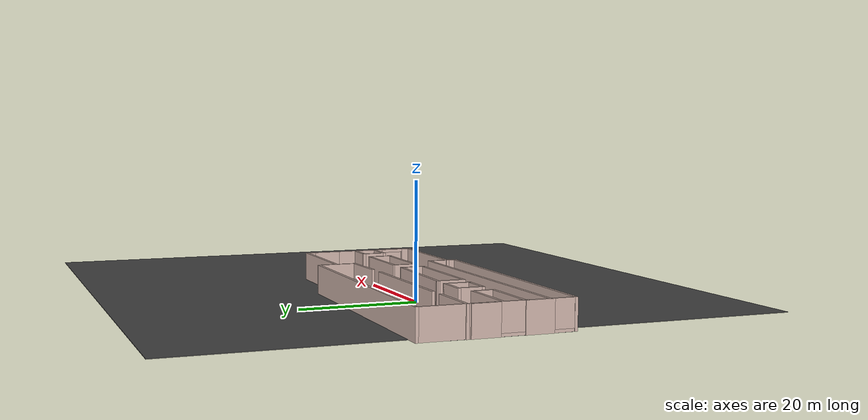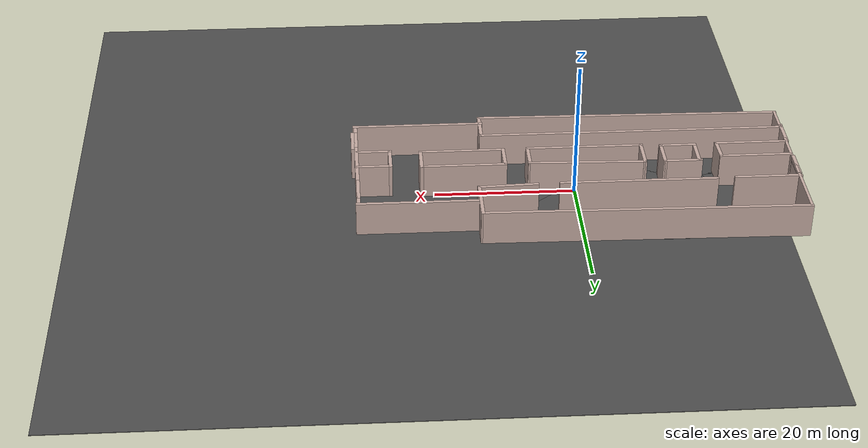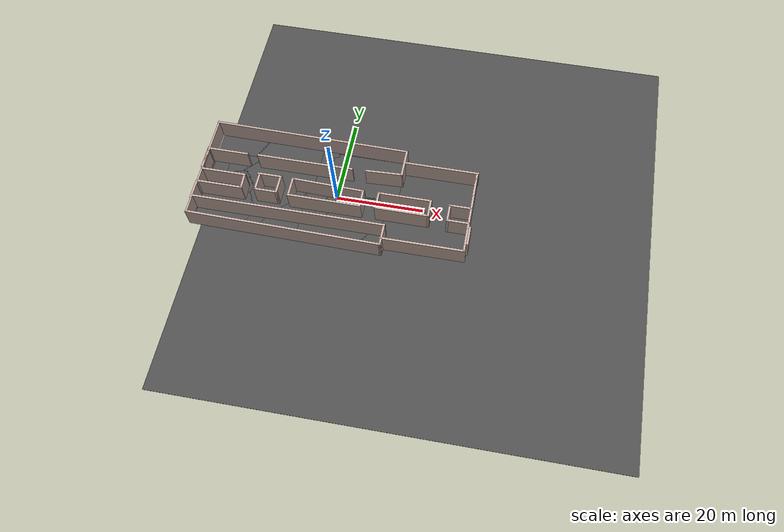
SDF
<?xml version='1.0'?>
<sdf version='1.6'>
  <model name='engineering_815'>
    <link name='Wall_345'>
      <pose frame=''>-30.9928 0.350371 0 0 0 -1.5708</pose>
      <self_collide>0</self_collide>
      <kinematic>0</kinematic>
      <visual name='Wall_345_Visual_3'>
        <pose frame=''>10.2836 0 2.75 0 -0 0</pose>
        <geometry>
          <box>
            <size>4.43242 0.4 4.5</size>
          </box>
        </geometry>
        <material>
          <script>
            <uri>file://media/materials/scripts/gazebo.material</uri>
            <name>Gazebo/Grey</name>
          </script>
          <ambient>0.760784 0.662745 0.627451 1</ambient>
          <diffuse>0.7 0.7 0.7 1</diffuse>
          <specular>0.01 0.01 0.01 1</specular>
          <emissive>0 0 0 1</emissive>
        </material>
        <cast_shadows>1</cast_shadows>
        <transparency>0</transparency>
      </visual>
      <visual name='Wall_345_Visual_2'>
        <pose frame=''>2.46579 0 2.75 0 -0 0</pose>
        <geometry>
          <box>
            <size>5.20312 0.4 4.5</size>
          </box>
        </geometry>
        <material>
          <script>
            <uri>file://media/materials/scripts/gazebo.material</uri>
            <name>Gazebo/Grey</name>
          </script>
          <ambient>0.760784 0.662745 0.627451 1</ambient>
          <diffuse>0.7 0.7 0.7 1</diffuse>
          <specular>0.01 0.01 0.01 1</specular>
          <emissive>0 0 0 1</emissive>
        </material>
        <cast_shadows>1</cast_shadows>
        <transparency>0</transparency>
      </visual>
      <visual name='Wall_345_Visual_4'>
        <pose frame=''>-2.13577 0 4.75 0 -0 0</pose>
        <geometry>
          <box>
            <size>4 0.4 0.5</size>
          </box>
        </geometry>
        <material>
          <script>
            <uri>file://media/materials/scripts/gazebo.material</uri>
            <name>Gazebo/Grey</name>
          </script>
          <ambient>0.760784 0.662745 0.627451 1</ambient>
          <diffuse>0.7 0.7 0.7 1</diffuse>
          <specular>0.01 0.01 0.01 1</specular>
          <emissive>0 0 0 1</emissive>
        </material>
        <cast_shadows>1</cast_shadows>
        <transparency>0</transparency>
      </visual>
      <visual name='Wall_345_Visual_1'>
        <pose frame=''>4.182 0 0.25 0 -0 0</pose>
        <geometry>
          <box>
            <size>16.6355 0.4 0.5</size>
          </box>
        </geometry>
        <material>
          <script>
            <uri>file://media/materials/scripts/gazebo.material</uri>
            <name>Gazebo/Grey</name>
          </script>
          <ambient>0.760784 0.662745 0.627451 1</ambient>
          <diffuse>0.7 0.7 0.7 1</diffuse>
          <specular>0.01 0.01 0.01 1</specular>
          <emissive>0 0 0 1</emissive>
        </material>
        <cast_shadows>1</cast_shadows>
        <transparency>0</transparency>
      </visual>
      <visual name='Wall_345_Visual_0'>
        <pose frame=''>-8.31777 0 2.5 0 -0 0</pose>
        <geometry>
          <box>
            <size>8.36401 0.4 5</size>
          </box>
        </geometry>
        <material>
          <script>
            <uri>file://media/materials/scripts/gazebo.material</uri>
            <name>Gazebo/Grey</name>
          </script>
          <ambient>0.760784 0.662745 0.627451 1</ambient>
          <diffuse>0.7 0.7 0.7 1</diffuse>
          <specular>0.01 0.01 0.01 1</specular>
          <emissive>0 0 0 1</emissive>
        </material>
        <cast_shadows>1</cast_shadows>
        <transparency>0</transparency>
      </visual>
      <collision name='Wall_345_Collision_4'>
        <laser_retro>0</laser_retro>
        <max_contacts>10</max_contacts>
        <pose frame=''>-2.13577 0 4.75 0 -0 0</pose>
        <geometry>
          <box>
            <size>4 0.4 0.5</size>
          </box>
        </geometry>
        <surface>
          <friction>
            <ode>
              <mu>1</mu>
              <mu2>1</mu2>
              <fdir1>0 0 0</fdir1>
              <slip1>0</slip1>
              <slip2>0</slip2>
            </ode>
            <torsional>
              <coefficient>1</coefficient>
              <patch_radius>0</patch_radius>
              <surface_radius>0</surface_radius>
              <use_patch_radius>1</use_patch_radius>
              <ode>
                <slip>0</slip>
              </ode>
            </torsional>
          </friction>
          <bounce>
            <restitution_coefficient>0</restitution_coefficient>
            <threshold>1e+06</threshold>
          </bounce>
          <contact>
            <collide_without_contact>0</collide_without_contact>
            <collide_without_contact_bitmask>1</collide_without_contact_bitmask>
            <collide_bitmask>1</collide_bitmask>
            <ode>
              <soft_cfm>0</soft_cfm>
              <soft_erp>0.2</soft_erp>
              <kp>1e+13</kp>
              <kd>1</kd>
              <max_vel>0.01</max_vel>
              <min_depth>0</min_depth>
            </ode>
            <bullet>
              <split_impulse>1</split_impulse>
              <split_impulse_penetration_threshold>-0.01</split_impulse_penetration_threshold>
              <soft_cfm>0</soft_cfm>
              <soft_erp>0.2</soft_erp>
              <kp>1e+13</kp>
              <kd>1</kd>
            </bullet>
          </contact>
        </surface>
      </collision>
      <collision name='Wall_345_Collision_3'>
        <laser_retro>0</laser_retro>
        <max_contacts>10</max_contacts>
        <pose frame=''>10.2836 0 2.75 0 -0 0</pose>
        <geometry>
          <box>
            <size>4.43242 0.4 4.5</size>
          </box>
        </geometry>
        <surface>
          <friction>
            <ode>
              <mu>1</mu>
              <mu2>1</mu2>
              <fdir1>0 0 0</fdir1>
              <slip1>0</slip1>
              <slip2>0</slip2>
            </ode>
            <torsional>
              <coefficient>1</coefficient>
              <patch_radius>0</patch_radius>
              <surface_radius>0</surface_radius>
              <use_patch_radius>1</use_patch_radius>
              <ode>
                <slip>0</slip>
              </ode>
            </torsional>
          </friction>
          <bounce>
            <restitution_coefficient>0</restitution_coefficient>
            <threshold>1e+06</threshold>
          </bounce>
          <contact>
            <collide_without_contact>0</collide_without_contact>
            <collide_without_contact_bitmask>1</collide_without_contact_bitmask>
            <collide_bitmask>1</collide_bitmask>
            <ode>
              <soft_cfm>0</soft_cfm>
              <soft_erp>0.2</soft_erp>
              <kp>1e+13</kp>
              <kd>1</kd>
              <max_vel>0.01</max_vel>
              <min_depth>0</min_depth>
            </ode>
            <bullet>
              <split_impulse>1</split_impulse>
              <split_impulse_penetration_threshold>-0.01</split_impulse_penetration_threshold>
              <soft_cfm>0</soft_cfm>
              <soft_erp>0.2</soft_erp>
              <kp>1e+13</kp>
              <kd>1</kd>
            </bullet>
          </contact>
        </surface>
      </collision>
      <collision name='Wall_345_Collision_1'>
        <laser_retro>0</laser_retro>
        <max_contacts>10</max_contacts>
        <pose frame=''>4.182 0 0.25 0 -0 0</pose>
        <geometry>
          <box>
            <size>16.6355 0.4 0.5</size>
          </box>
        </geometry>
        <surface>
          <friction>
            <ode>
              <mu>1</mu>
              <mu2>1</mu2>
              <fdir1>0 0 0</fdir1>
              <slip1>0</slip1>
              <slip2>0</slip2>
            </ode>
            <torsional>
              <coefficient>1</coefficient>
              <patch_radius>0</patch_radius>
              <surface_radius>0</surface_radius>
              <use_patch_radius>1</use_patch_radius>
              <ode>
                <slip>0</slip>
              </ode>
            </torsional>
          </friction>
          <bounce>
            <restitution_coefficient>0</restitution_coefficient>
            <threshold>1e+06</threshold>
          </bounce>
          <contact>
            <collide_without_contact>0</collide_without_contact>
            <collide_without_contact_bitmask>1</collide_without_contact_bitmask>
            <collide_bitmask>1</collide_bitmask>
            <ode>
              <soft_cfm>0</soft_cfm>
              <soft_erp>0.2</soft_erp>
              <kp>1e+13</kp>
              <kd>1</kd>
              <max_vel>0.01</max_vel>
              <min_depth>0</min_depth>
            </ode>
            <bullet>
              <split_impulse>1</split_impulse>
              <split_impulse_penetration_threshold>-0.01</split_impulse_penetration_threshold>
              <soft_cfm>0</soft_cfm>
              <soft_erp>0.2</soft_erp>
              <kp>1e+13</kp>
              <kd>1</kd>
            </bullet>
          </contact>
        </surface>
      </collision>
      <collision name='Wall_345_Collision_2'>
        <laser_retro>0</laser_retro>
        <max_contacts>10</max_contacts>
        <pose frame=''>2.46579 0 2.75 0 -0 0</pose>
        <geometry>
          <box>
            <size>5.20312 0.4 4.5</size>
          </box>
        </geometry>
        <surface>
          <friction>
            <ode>
              <mu>1</mu>
              <mu2>1</mu2>
              <fdir1>0 0 0</fdir1>
              <slip1>0</slip1>
              <slip2>0</slip2>
            </ode>
            <torsional>
              <coefficient>1</coefficient>
              <patch_radius>0</patch_radius>
              <surface_radius>0</surface_radius>
              <use_patch_radius>1</use_patch_radius>
              <ode>
                <slip>0</slip>
              </ode>
            </torsional>
          </friction>
          <bounce>
            <restitution_coefficient>0</restitution_coefficient>
            <threshold>1e+06</threshold>
          </bounce>
          <contact>
            <collide_without_contact>0</collide_without_contact>
            <collide_without_contact_bitmask>1</collide_without_contact_bitmask>
            <collide_bitmask>1</collide_bitmask>
            <ode>
              <soft_cfm>0</soft_cfm>
              <soft_erp>0.2</soft_erp>
              <kp>1e+13</kp>
              <kd>1</kd>
              <max_vel>0.01</max_vel>
              <min_depth>0</min_depth>
            </ode>
            <bullet>
              <split_impulse>1</split_impulse>
              <split_impulse_penetration_threshold>-0.01</split_impulse_penetration_threshold>
              <soft_cfm>0</soft_cfm>
              <soft_erp>0.2</soft_erp>
              <kp>1e+13</kp>
              <kd>1</kd>
            </bullet>
          </contact>
        </surface>
      </collision>
      <collision name='Wall_345_Collision_0'>
        <laser_retro>0</laser_retro>
        <max_contacts>10</max_contacts>
        <pose frame=''>-8.31777 0 2.5 0 -0 0</pose>
        <geometry>
          <box>
            <size>8.36401 0.4 5</size>
          </box>
        </geometry>
        <surface>
          <friction>
            <ode>
              <mu>1</mu>
              <mu2>1</mu2>
              <fdir1>0 0 0</fdir1>
              <slip1>0</slip1>
              <slip2>0</slip2>
            </ode>
            <torsional>
              <coefficient>1</coefficient>
              <patch_radius>0</patch_radius>
              <surface_radius>0</surface_radius>
              <use_patch_radius>1</use_patch_radius>
              <ode>
                <slip>0</slip>
              </ode>
            </torsional>
          </friction>
          <bounce>
            <restitution_coefficient>0</restitution_coefficient>
            <threshold>1e+06</threshold>
          </bounce>
          <contact>
            <collide_without_contact>0</collide_without_contact>
            <collide_without_contact_bitmask>1</collide_without_contact_bitmask>
            <collide_bitmask>1</collide_bitmask>
            <ode>
              <soft_cfm>0</soft_cfm>
              <soft_erp>0.2</soft_erp>
              <kp>1e+13</kp>
              <kd>1</kd>
              <max_vel>0.01</max_vel>
              <min_depth>0</min_depth>
            </ode>
            <bullet>
              <split_impulse>1</split_impulse>
              <split_impulse_penetration_threshold>-0.01</split_impulse_penetration_threshold>
              <soft_cfm>0</soft_cfm>
              <soft_erp>0.2</soft_erp>
              <kp>1e+13</kp>
              <kd>1</kd>
            </bullet>
          </contact>
        </surface>
      </collision>
    </link>
    <link name='Wall_348'>
      <pose frame=''>14.1272 8.89037 0 0 -0 1.5708</pose>
      <self_collide>0</self_collide>
      <kinematic>0</kinematic>
      <visual name='Wall_348_Visual'>
        <pose frame=''>0 0 2.5 0 -0 0</pose>
        <geometry>
          <box>
            <size>6.85 0.5 5</size>
          </box>
        </geometry>
        <material>
          <script>
            <uri>file://media/materials/scripts/gazebo.material</uri>
            <name>Gazebo/Grey</name>
          </script>
          <ambient>0.760784 0.662745 0.627451 1</ambient>
          <diffuse>0.7 0.7 0.7 1</diffuse>
          <specular>0.01 0.01 0.01 1</specular>
          <emissive>0 0 0 1</emissive>
        </material>
        <cast_shadows>1</cast_shadows>
        <transparency>0</transparency>
      </visual>
      <collision name='Wall_348_Collision'>
        <laser_retro>0</laser_retro>
        <max_contacts>10</max_contacts>
        <pose frame=''>0 0 2.5 0 -0 0</pose>
        <geometry>
          <box>
            <size>6.85 0.5 5</size>
          </box>
        </geometry>
        <surface>
          <friction>
            <ode>
              <mu>1</mu>
              <mu2>1</mu2>
              <fdir1>0 0 0</fdir1>
              <slip1>0</slip1>
              <slip2>0</slip2>
            </ode>
            <torsional>
              <coefficient>1</coefficient>
              <patch_radius>0</patch_radius>
              <surface_radius>0</surface_radius>
              <use_patch_radius>1</use_patch_radius>
              <ode>
                <slip>0</slip>
              </ode>
            </torsional>
          </friction>
          <bounce>
            <restitution_coefficient>0</restitution_coefficient>
            <threshold>1e+06</threshold>
          </bounce>
          <contact>
            <collide_without_contact>0</collide_without_contact>
            <collide_without_contact_bitmask>1</collide_without_contact_bitmask>
            <collide_bitmask>1</collide_bitmask>
            <ode>
              <soft_cfm>0</soft_cfm>
              <soft_erp>0.2</soft_erp>
              <kp>1e+13</kp>
              <kd>1</kd>
              <max_vel>0.01</max_vel>
              <min_depth>0</min_depth>
            </ode>
            <bullet>
              <split_impulse>1</split_impulse>
              <split_impulse_penetration_threshold>-0.01</split_impulse_penetration_threshold>
              <soft_cfm>0</soft_cfm>
              <soft_erp>0.2</soft_erp>
              <kp>1e+13</kp>
              <kd>1</kd>
            </bullet>
          </contact>
        </surface>
      </collision>
    </link>
    <link name='Wall_349'>
      <pose frame=''>-8.43279 12.3579 0 0 -0 3.12863</pose>
      <self_collide>0</self_collide>
      <kinematic>0</kinematic>
      <visual name='Wall_349_Visual'>
        <pose frame=''>0 0 2.5 0 -0 0</pose>
        <geometry>
          <box>
            <size>45.6238 0.5 5</size>
          </box>
        </geometry>
        <material>
          <script>
            <uri>file://media/materials/scripts/gazebo.material</uri>
            <name>Gazebo/Grey</name>
          </script>
          <ambient>0.760784 0.662745 0.627451 1</ambient>
          <diffuse>0.7 0.7 0.7 1</diffuse>
          <specular>0.01 0.01 0.01 1</specular>
          <emissive>0 0 0 1</emissive>
        </material>
        <cast_shadows>1</cast_shadows>
        <transparency>0</transparency>
      </visual>
      <collision name='Wall_349_Collision'>
        <laser_retro>0</laser_retro>
        <max_contacts>10</max_contacts>
        <pose frame=''>0 0 2.5 0 -0 0</pose>
        <geometry>
          <box>
            <size>45.6238 0.5 5</size>
          </box>
        </geometry>
        <surface>
          <friction>
            <ode>
              <mu>1</mu>
              <mu2>1</mu2>
              <fdir1>0 0 0</fdir1>
              <slip1>0</slip1>
              <slip2>0</slip2>
            </ode>
            <torsional>
              <coefficient>1</coefficient>
              <patch_radius>0</patch_radius>
              <surface_radius>0</surface_radius>
              <use_patch_radius>1</use_patch_radius>
              <ode>
                <slip>0</slip>
              </ode>
            </torsional>
          </friction>
          <bounce>
            <restitution_coefficient>0</restitution_coefficient>
            <threshold>1e+06</threshold>
          </bounce>
          <contact>
            <collide_without_contact>0</collide_without_contact>
            <collide_without_contact_bitmask>1</collide_without_contact_bitmask>
            <collide_bitmask>1</collide_bitmask>
            <ode>
              <soft_cfm>0</soft_cfm>
              <soft_erp>0.2</soft_erp>
              <kp>1e+13</kp>
              <kd>1</kd>
              <max_vel>0.01</max_vel>
              <min_depth>0</min_depth>
            </ode>
            <bullet>
              <split_impulse>1</split_impulse>
              <split_impulse_penetration_threshold>-0.01</split_impulse_penetration_threshold>
              <soft_cfm>0</soft_cfm>
              <soft_erp>0.2</soft_erp>
              <kp>1e+13</kp>
              <kd>1</kd>
            </bullet>
          </contact>
        </surface>
      </collision>
    </link>
    <link name='Wall_351'>
      <pose frame=''>-25.8755 -0.471856 0 0 -0 0</pose>
      <self_collide>0</self_collide>
      <kinematic>0</kinematic>
      <visual name='Wall_351_Visual'>
        <pose frame=''>0 0 2.5 0 -0 0</pose>
        <geometry>
          <box>
            <size>10.35 0.5 5</size>
          </box>
        </geometry>
        <material>
          <script>
            <uri>file://media/materials/scripts/gazebo.material</uri>
            <name>Gazebo/Grey</name>
          </script>
          <ambient>0.760784 0.662745 0.627451 1</ambient>
          <diffuse>0.7 0.7 0.7 1</diffuse>
          <specular>0.01 0.01 0.01 1</specular>
          <emissive>0 0 0 1</emissive>
        </material>
        <cast_shadows>1</cast_shadows>
        <transparency>0</transparency>
      </visual>
      <collision name='Wall_351_Collision'>
        <laser_retro>0</laser_retro>
        <max_contacts>10</max_contacts>
        <pose frame=''>0 0 2.5 0 -0 0</pose>
        <geometry>
          <box>
            <size>10.35 0.5 5</size>
          </box>
        </geometry>
        <surface>
          <friction>
            <ode>
              <mu>1</mu>
              <mu2>1</mu2>
              <fdir1>0 0 0</fdir1>
              <slip1>0</slip1>
              <slip2>0</slip2>
            </ode>
            <torsional>
              <coefficient>1</coefficient>
              <patch_radius>0</patch_radius>
              <surface_radius>0</surface_radius>
              <use_patch_radius>1</use_patch_radius>
              <ode>
                <slip>0</slip>
              </ode>
            </torsional>
          </friction>
          <bounce>
            <restitution_coefficient>0</restitution_coefficient>
            <threshold>1e+06</threshold>
          </bounce>
          <contact>
            <collide_without_contact>0</collide_without_contact>
            <collide_without_contact_bitmask>1</collide_without_contact_bitmask>
            <collide_bitmask>1</collide_bitmask>
            <ode>
              <soft_cfm>0</soft_cfm>
              <soft_erp>0.2</soft_erp>
              <kp>1e+13</kp>
              <kd>1</kd>
              <max_vel>0.01</max_vel>
              <min_depth>0</min_depth>
            </ode>
            <bullet>
              <split_impulse>1</split_impulse>
              <split_impulse_penetration_threshold>-0.01</split_impulse_penetration_threshold>
              <soft_cfm>0</soft_cfm>
              <soft_erp>0.2</soft_erp>
              <kp>1e+13</kp>
              <kd>1</kd>
            </bullet>
          </contact>
        </surface>
      </collision>
    </link>
    <link name='Wall_352'>
      <pose frame=''>-20.8797 -2.17745 0 0 0 -1.52833</pose>
      <self_collide>0</self_collide>
      <kinematic>0</kinematic>
      <visual name='Wall_352_Visual'>
        <pose frame=''>0 0 2.5 0 -0 0</pose>
        <geometry>
          <box>
            <size>3.83327 0.5 5</size>
          </box>
        </geometry>
        <material>
          <script>
            <uri>file://media/materials/scripts/gazebo.material</uri>
            <name>Gazebo/Grey</name>
          </script>
          <ambient>0.760784 0.662745 0.627451 1</ambient>
          <diffuse>0.7 0.7 0.7 1</diffuse>
          <specular>0.01 0.01 0.01 1</specular>
          <emissive>0 0 0 1</emissive>
        </material>
        <cast_shadows>1</cast_shadows>
        <transparency>0</transparency>
      </visual>
      <collision name='Wall_352_Collision'>
        <laser_retro>0</laser_retro>
        <max_contacts>10</max_contacts>
        <pose frame=''>0 0 2.5 0 -0 0</pose>
        <geometry>
          <box>
            <size>3.83327 0.5 5</size>
          </box>
        </geometry>
        <surface>
          <friction>
            <ode>
              <mu>1</mu>
              <mu2>1</mu2>
              <fdir1>0 0 0</fdir1>
              <slip1>0</slip1>
              <slip2>0</slip2>
            </ode>
            <torsional>
              <coefficient>1</coefficient>
              <patch_radius>0</patch_radius>
              <surface_radius>0</surface_radius>
              <use_patch_radius>1</use_patch_radius>
              <ode>
                <slip>0</slip>
              </ode>
            </torsional>
          </friction>
          <bounce>
            <restitution_coefficient>0</restitution_coefficient>
            <threshold>1e+06</threshold>
          </bounce>
          <contact>
            <collide_without_contact>0</collide_without_contact>
            <collide_without_contact_bitmask>1</collide_without_contact_bitmask>
            <collide_bitmask>1</collide_bitmask>
            <ode>
              <soft_cfm>0</soft_cfm>
              <soft_erp>0.2</soft_erp>
              <kp>1e+13</kp>
              <kd>1</kd>
              <max_vel>0.01</max_vel>
              <min_depth>0</min_depth>
            </ode>
            <bullet>
              <split_impulse>1</split_impulse>
              <split_impulse_penetration_threshold>-0.01</split_impulse_penetration_threshold>
              <soft_cfm>0</soft_cfm>
              <soft_erp>0.2</soft_erp>
              <kp>1e+13</kp>
              <kd>1</kd>
            </bullet>
          </contact>
        </surface>
      </collision>
    </link>
    <link name='Wall_353'>
      <pose frame=''>-25.7744 -3.88304 0 0 -0 3.14159</pose>
      <self_collide>0</self_collide>
      <kinematic>0</kinematic>
      <visual name='Wall_353_Visual'>
        <pose frame=''>0 0 2.5 0 -0 0</pose>
        <geometry>
          <box>
            <size>10.35 0.5 5</size>
          </box>
        </geometry>
        <material>
          <script>
            <uri>file://media/materials/scripts/gazebo.material</uri>
            <name>Gazebo/Grey</name>
          </script>
          <ambient>0.760784 0.662745 0.627451 1</ambient>
          <diffuse>0.7 0.7 0.7 1</diffuse>
          <specular>0.01 0.01 0.01 1</specular>
          <emissive>0 0 0 1</emissive>
        </material>
        <cast_shadows>1</cast_shadows>
        <transparency>0</transparency>
      </visual>
      <collision name='Wall_353_Collision'>
        <laser_retro>0</laser_retro>
        <max_contacts>10</max_contacts>
        <pose frame=''>0 0 2.5 0 -0 0</pose>
        <geometry>
          <box>
            <size>10.35 0.5 5</size>
          </box>
        </geometry>
        <surface>
          <friction>
            <ode>
              <mu>1</mu>
              <mu2>1</mu2>
              <fdir1>0 0 0</fdir1>
              <slip1>0</slip1>
              <slip2>0</slip2>
            </ode>
            <torsional>
              <coefficient>1</coefficient>
              <patch_radius>0</patch_radius>
              <surface_radius>0</surface_radius>
              <use_patch_radius>1</use_patch_radius>
              <ode>
                <slip>0</slip>
              </ode>
            </torsional>
          </friction>
          <bounce>
            <restitution_coefficient>0</restitution_coefficient>
            <threshold>1e+06</threshold>
          </bounce>
          <contact>
            <collide_without_contact>0</collide_without_contact>
            <collide_without_contact_bitmask>1</collide_without_contact_bitmask>
            <collide_bitmask>1</collide_bitmask>
            <ode>
              <soft_cfm>0</soft_cfm>
              <soft_erp>0.2</soft_erp>
              <kp>1e+13</kp>
              <kd>1</kd>
              <max_vel>0.01</max_vel>
              <min_depth>0</min_depth>
            </ode>
            <bullet>
              <split_impulse>1</split_impulse>
              <split_impulse_penetration_threshold>-0.01</split_impulse_penetration_threshold>
              <soft_cfm>0</soft_cfm>
              <soft_erp>0.2</soft_erp>
              <kp>1e+13</kp>
              <kd>1</kd>
            </bullet>
          </contact>
        </surface>
      </collision>
    </link>
    <link name='Wall_355'>
      <pose frame=''>-9.11879 -7.79963 0 0 -0 0</pose>
      <self_collide>0</self_collide>
      <kinematic>0</kinematic>
      <visual name='Wall_355_Visual'>
        <pose frame=''>0 0 2.5 0 -0 0</pose>
        <geometry>
          <box>
            <size>44.3504 0.5 5</size>
          </box>
        </geometry>
        <material>
          <script>
            <uri>file://media/materials/scripts/gazebo.material</uri>
            <name>Gazebo/Grey</name>
          </script>
          <ambient>0.760784 0.662745 0.627451 1</ambient>
          <diffuse>0.7 0.7 0.7 1</diffuse>
          <specular>0.01 0.01 0.01 1</specular>
          <emissive>0 0 0 1</emissive>
        </material>
        <cast_shadows>1</cast_shadows>
        <transparency>0</transparency>
      </visual>
      <collision name='Wall_355_Collision'>
        <laser_retro>0</laser_retro>
        <max_contacts>10</max_contacts>
        <pose frame=''>0 0 2.5 0 -0 0</pose>
        <geometry>
          <box>
            <size>44.3504 0.5 5</size>
          </box>
        </geometry>
        <surface>
          <friction>
            <ode>
              <mu>1</mu>
              <mu2>1</mu2>
              <fdir1>0 0 0</fdir1>
              <slip1>0</slip1>
              <slip2>0</slip2>
            </ode>
            <torsional>
              <coefficient>1</coefficient>
              <patch_radius>0</patch_radius>
              <surface_radius>0</surface_radius>
              <use_patch_radius>1</use_patch_radius>
              <ode>
                <slip>0</slip>
              </ode>
            </torsional>
          </friction>
          <bounce>
            <restitution_coefficient>0</restitution_coefficient>
            <threshold>1e+06</threshold>
          </bounce>
          <contact>
            <collide_without_contact>0</collide_without_contact>
            <collide_without_contact_bitmask>1</collide_without_contact_bitmask>
            <collide_bitmask>1</collide_bitmask>
            <ode>
              <soft_cfm>0</soft_cfm>
              <soft_erp>0.2</soft_erp>
              <kp>1e+13</kp>
              <kd>1</kd>
              <max_vel>0.01</max_vel>
              <min_depth>0</min_depth>
            </ode>
            <bullet>
              <split_impulse>1</split_impulse>
              <split_impulse_penetration_threshold>-0.01</split_impulse_penetration_threshold>
              <soft_cfm>0</soft_cfm>
              <soft_erp>0.2</soft_erp>
              <kp>1e+13</kp>
              <kd>1</kd>
            </bullet>
          </contact>
        </surface>
      </collision>
    </link>
    <link name='Wall_356'>
      <pose frame=''>12.8062 -10.2246 0 0 0 -1.5708</pose>
      <self_collide>0</self_collide>
      <kinematic>0</kinematic>
      <visual name='Wall_356_Visual'>
        <pose frame=''>0 0 2.5 0 -0 0</pose>
        <geometry>
          <box>
            <size>5.34955 0.5 5</size>
          </box>
        </geometry>
        <material>
          <script>
            <uri>file://media/materials/scripts/gazebo.material</uri>
            <name>Gazebo/Grey</name>
          </script>
          <ambient>0.760784 0.662745 0.627451 1</ambient>
          <diffuse>0.7 0.7 0.7 1</diffuse>
          <specular>0.01 0.01 0.01 1</specular>
          <emissive>0 0 0 1</emissive>
        </material>
        <cast_shadows>1</cast_shadows>
        <transparency>0</transparency>
      </visual>
      <collision name='Wall_356_Collision'>
        <laser_retro>0</laser_retro>
        <max_contacts>10</max_contacts>
        <pose frame=''>0 0 2.5 0 -0 0</pose>
        <geometry>
          <box>
            <size>5.34955 0.5 5</size>
          </box>
        </geometry>
        <surface>
          <friction>
            <ode>
              <mu>1</mu>
              <mu2>1</mu2>
              <fdir1>0 0 0</fdir1>
              <slip1>0</slip1>
              <slip2>0</slip2>
            </ode>
            <torsional>
              <coefficient>1</coefficient>
              <patch_radius>0</patch_radius>
              <surface_radius>0</surface_radius>
              <use_patch_radius>1</use_patch_radius>
              <ode>
                <slip>0</slip>
              </ode>
            </torsional>
          </friction>
          <bounce>
            <restitution_coefficient>0</restitution_coefficient>
            <threshold>1e+06</threshold>
          </bounce>
          <contact>
            <collide_without_contact>0</collide_without_contact>
            <collide_without_contact_bitmask>1</collide_without_contact_bitmask>
            <collide_bitmask>1</collide_bitmask>
            <ode>
              <soft_cfm>0</soft_cfm>
              <soft_erp>0.2</soft_erp>
              <kp>1e+13</kp>
              <kd>1</kd>
              <max_vel>0.01</max_vel>
              <min_depth>0</min_depth>
            </ode>
            <bullet>
              <split_impulse>1</split_impulse>
              <split_impulse_penetration_threshold>-0.01</split_impulse_penetration_threshold>
              <soft_cfm>0</soft_cfm>
              <soft_erp>0.2</soft_erp>
              <kp>1e+13</kp>
              <kd>1</kd>
            </bullet>
          </contact>
        </surface>
      </collision>
    </link>
    <link name='Wall_357'>
      <pose frame=''>-9.09328 -12.2996 0 0 -0 3.12561</pose>
      <self_collide>0</self_collide>
      <kinematic>0</kinematic>
      <visual name='Wall_357_Visual'>
        <pose frame=''>0 0 2.5 0 -0 0</pose>
        <geometry>
          <box>
            <size>44.3046 0.5 5</size>
          </box>
        </geometry>
        <material>
          <script>
            <uri>file://media/materials/scripts/gazebo.material</uri>
            <name>Gazebo/Grey</name>
          </script>
          <ambient>0.760784 0.662745 0.627451 1</ambient>
          <diffuse>0.7 0.7 0.7 1</diffuse>
          <specular>0.01 0.01 0.01 1</specular>
          <emissive>0 0 0 1</emissive>
        </material>
        <cast_shadows>1</cast_shadows>
        <transparency>0</transparency>
      </visual>
      <collision name='Wall_357_Collision'>
        <laser_retro>0</laser_retro>
        <max_contacts>10</max_contacts>
        <pose frame=''>0 0 2.5 0 -0 0</pose>
        <geometry>
          <box>
            <size>44.3046 0.5 5</size>
          </box>
        </geometry>
        <surface>
          <friction>
            <ode>
              <mu>1</mu>
              <mu2>1</mu2>
              <fdir1>0 0 0</fdir1>
              <slip1>0</slip1>
              <slip2>0</slip2>
            </ode>
            <torsional>
              <coefficient>1</coefficient>
              <patch_radius>0</patch_radius>
              <surface_radius>0</surface_radius>
              <use_patch_radius>1</use_patch_radius>
              <ode>
                <slip>0</slip>
              </ode>
            </torsional>
          </friction>
          <bounce>
            <restitution_coefficient>0</restitution_coefficient>
            <threshold>1e+06</threshold>
          </bounce>
          <contact>
            <collide_without_contact>0</collide_without_contact>
            <collide_without_contact_bitmask>1</collide_without_contact_bitmask>
            <collide_bitmask>1</collide_bitmask>
            <ode>
              <soft_cfm>0</soft_cfm>
              <soft_erp>0.2</soft_erp>
              <kp>1e+13</kp>
              <kd>1</kd>
              <max_vel>0.01</max_vel>
              <min_depth>0</min_depth>
            </ode>
            <bullet>
              <split_impulse>1</split_impulse>
              <split_impulse_penetration_threshold>-0.01</split_impulse_penetration_threshold>
              <soft_cfm>0</soft_cfm>
              <soft_erp>0.2</soft_erp>
              <kp>1e+13</kp>
              <kd>1</kd>
            </bullet>
          </contact>
        </surface>
      </collision>
    </link>
    <link name='Wall_359'>
      <pose frame=''>-17.5998 -1.64163 0 0 0 -1.5708</pose>
      <self_collide>0</self_collide>
      <kinematic>0</kinematic>
      <visual name='Wall_359_Visual'>
        <pose frame=''>0 0 2.5 0 -0 0</pose>
        <geometry>
          <box>
            <size>4.59973 0.5 5</size>
          </box>
        </geometry>
        <material>
          <script>
            <uri>file://media/materials/scripts/gazebo.material</uri>
            <name>Gazebo/Grey</name>
          </script>
          <ambient>0.760784 0.662745 0.627451 1</ambient>
          <diffuse>0.7 0.7 0.7 1</diffuse>
          <specular>0.01 0.01 0.01 1</specular>
          <emissive>0 0 0 1</emissive>
        </material>
        <cast_shadows>1</cast_shadows>
        <transparency>0</transparency>
      </visual>
      <collision name='Wall_359_Collision'>
        <laser_retro>0</laser_retro>
        <max_contacts>10</max_contacts>
        <pose frame=''>0 0 2.5 0 -0 0</pose>
        <geometry>
          <box>
            <size>4.59973 0.5 5</size>
          </box>
        </geometry>
        <surface>
          <friction>
            <ode>
              <mu>1</mu>
              <mu2>1</mu2>
              <fdir1>0 0 0</fdir1>
              <slip1>0</slip1>
              <slip2>0</slip2>
            </ode>
            <torsional>
              <coefficient>1</coefficient>
              <patch_radius>0</patch_radius>
              <surface_radius>0</surface_radius>
              <use_patch_radius>1</use_patch_radius>
              <ode>
                <slip>0</slip>
              </ode>
            </torsional>
          </friction>
          <bounce>
            <restitution_coefficient>0</restitution_coefficient>
            <threshold>1e+06</threshold>
          </bounce>
          <contact>
            <collide_without_contact>0</collide_without_contact>
            <collide_without_contact_bitmask>1</collide_without_contact_bitmask>
            <collide_bitmask>1</collide_bitmask>
            <ode>
              <soft_cfm>0</soft_cfm>
              <soft_erp>0.2</soft_erp>
              <kp>1e+13</kp>
              <kd>1</kd>
              <max_vel>0.01</max_vel>
              <min_depth>0</min_depth>
            </ode>
            <bullet>
              <split_impulse>1</split_impulse>
              <split_impulse_penetration_threshold>-0.01</split_impulse_penetration_threshold>
              <soft_cfm>0</soft_cfm>
              <soft_erp>0.2</soft_erp>
              <kp>1e+13</kp>
              <kd>1</kd>
            </bullet>
          </contact>
        </surface>
      </collision>
    </link>
    <link name='Wall_359_clone'>
      <pose frame=''>-31.1334 2.28437 0 0 0 -1.5708</pose>
      <self_collide>0</self_collide>
      <kinematic>0</kinematic>
      <visual name='Wall_359_Visual'>
        <pose frame=''>0 0 2.5 0 -0 0</pose>
        <geometry>
          <box>
            <size>4.59973 0.5 5</size>
          </box>
        </geometry>
        <material>
          <script>
            <uri>file://media/materials/scripts/gazebo.material</uri>
            <name>Gazebo/Grey</name>
          </script>
          <ambient>0.760784 0.662745 0.627451 1</ambient>
          <diffuse>0.7 0.7 0.7 1</diffuse>
          <specular>0.01 0.01 0.01 1</specular>
          <emissive>0 0 0 1</emissive>
          <shader type='pixel'/>
        </material>
        <cast_shadows>1</cast_shadows>
        <transparency>0</transparency>
      </visual>
      <collision name='Wall_359_Collision'>
        <laser_retro>0</laser_retro>
        <max_contacts>10</max_contacts>
        <pose frame=''>0 0 2.5 0 -0 0</pose>
        <geometry>
          <box>
            <size>4.59973 0.5 5</size>
          </box>
        </geometry>
        <surface>
          <friction>
            <ode>
              <mu>1</mu>
              <mu2>1</mu2>
              <fdir1>0 0 0</fdir1>
              <slip1>0</slip1>
              <slip2>0</slip2>
            </ode>
            <torsional>
              <coefficient>1</coefficient>
              <patch_radius>0</patch_radius>
              <surface_radius>0</surface_radius>
              <use_patch_radius>1</use_patch_radius>
              <ode>
                <slip>0</slip>
              </ode>
            </torsional>
          </friction>
          <bounce>
            <restitution_coefficient>0</restitution_coefficient>
            <threshold>1e+06</threshold>
          </bounce>
          <contact>
            <collide_without_contact>0</collide_without_contact>
            <collide_without_contact_bitmask>1</collide_without_contact_bitmask>
            <collide_bitmask>1</collide_bitmask>
            <ode>
              <soft_cfm>0</soft_cfm>
              <soft_erp>0.2</soft_erp>
              <kp>1e+13</kp>
              <kd>1</kd>
              <max_vel>0.01</max_vel>
              <min_depth>0</min_depth>
            </ode>
            <bullet>
              <split_impulse>1</split_impulse>
              <split_impulse_penetration_threshold>-0.01</split_impulse_penetration_threshold>
              <soft_cfm>0</soft_cfm>
              <soft_erp>0.2</soft_erp>
              <kp>1e+13</kp>
              <kd>1</kd>
            </bullet>
          </contact>
        </surface>
      </collision>
    </link>
    <link name='Wall_359_clone_0'>
      <pose frame=''>-31.1127 -6.13704 0 0 0 -1.5708</pose>
      <self_collide>0</self_collide>
      <kinematic>0</kinematic>
      <visual name='Wall_359_Visual'>
        <pose frame=''>0 0 2.5 0 -0 0</pose>
        <geometry>
          <box>
            <size>4.59973 0.5 5</size>
          </box>
        </geometry>
        <material>
          <script>
            <uri>file://media/materials/scripts/gazebo.material</uri>
            <name>Gazebo/Grey</name>
          </script>
          <ambient>0.760784 0.662745 0.627451 1</ambient>
          <diffuse>0.7 0.7 0.7 1</diffuse>
          <specular>0.01 0.01 0.01 1</specular>
          <emissive>0 0 0 1</emissive>
          <shader type='pixel'/>
        </material>
        <cast_shadows>1</cast_shadows>
        <transparency>0</transparency>
      </visual>
      <collision name='Wall_359_Collision'>
        <laser_retro>0</laser_retro>
        <max_contacts>10</max_contacts>
        <pose frame=''>0 0 2.5 0 -0 0</pose>
        <geometry>
          <box>
            <size>4.59973 0.5 5</size>
          </box>
        </geometry>
        <surface>
          <friction>
            <ode>
              <mu>1</mu>
              <mu2>1</mu2>
              <fdir1>0 0 0</fdir1>
              <slip1>0</slip1>
              <slip2>0</slip2>
            </ode>
            <torsional>
              <coefficient>1</coefficient>
              <patch_radius>0</patch_radius>
              <surface_radius>0</surface_radius>
              <use_patch_radius>1</use_patch_radius>
              <ode>
                <slip>0</slip>
              </ode>
            </torsional>
          </friction>
          <bounce>
            <restitution_coefficient>0</restitution_coefficient>
            <threshold>1e+06</threshold>
          </bounce>
          <contact>
            <collide_without_contact>0</collide_without_contact>
            <collide_without_contact_bitmask>1</collide_without_contact_bitmask>
            <collide_bitmask>1</collide_bitmask>
            <ode>
              <soft_cfm>0</soft_cfm>
              <soft_erp>0.2</soft_erp>
              <kp>1e+13</kp>
              <kd>1</kd>
              <max_vel>0.01</max_vel>
              <min_depth>0</min_depth>
            </ode>
            <bullet>
              <split_impulse>1</split_impulse>
              <split_impulse_penetration_threshold>-0.01</split_impulse_penetration_threshold>
              <soft_cfm>0</soft_cfm>
              <soft_erp>0.2</soft_erp>
              <kp>1e+13</kp>
              <kd>1</kd>
            </bullet>
          </contact>
        </surface>
      </collision>
    </link>
    <link name='Wall_359_clone_1'>
      <pose frame=''>31.4492 -7.25835 0 0 0 -1.5708</pose>
      <self_collide>0</self_collide>
      <kinematic>0</kinematic>
      <visual name='Wall_359_Visual'>
        <pose frame=''>0 0 2.5 0 -0 0</pose>
        <geometry>
          <box>
            <size>4.59973 0.5 5</size>
          </box>
        </geometry>
        <material>
          <script>
            <uri>file://media/materials/scripts/gazebo.material</uri>
            <name>Gazebo/Grey</name>
          </script>
          <ambient>0.760784 0.662745 0.627451 1</ambient>
          <diffuse>0.7 0.7 0.7 1</diffuse>
          <specular>0.01 0.01 0.01 1</specular>
          <emissive>0 0 0 1</emissive>
          <shader type='pixel'/>
        </material>
        <cast_shadows>1</cast_shadows>
        <transparency>0</transparency>
      </visual>
      <collision name='Wall_359_Collision'>
        <laser_retro>0</laser_retro>
        <max_contacts>10</max_contacts>
        <pose frame=''>0 0 2.5 0 -0 0</pose>
        <geometry>
          <box>
            <size>4.59973 0.5 5</size>
          </box>
        </geometry>
        <surface>
          <friction>
            <ode>
              <mu>1</mu>
              <mu2>1</mu2>
              <fdir1>0 0 0</fdir1>
              <slip1>0</slip1>
              <slip2>0</slip2>
            </ode>
            <torsional>
              <coefficient>1</coefficient>
              <patch_radius>0</patch_radius>
              <surface_radius>0</surface_radius>
              <use_patch_radius>1</use_patch_radius>
              <ode>
                <slip>0</slip>
              </ode>
            </torsional>
          </friction>
          <bounce>
            <restitution_coefficient>0</restitution_coefficient>
            <threshold>1e+06</threshold>
          </bounce>
          <contact>
            <collide_without_contact>0</collide_without_contact>
            <collide_without_contact_bitmask>1</collide_without_contact_bitmask>
            <collide_bitmask>1</collide_bitmask>
            <ode>
              <soft_cfm>0</soft_cfm>
              <soft_erp>0.2</soft_erp>
              <kp>1e+13</kp>
              <kd>1</kd>
              <max_vel>0.01</max_vel>
              <min_depth>0</min_depth>
            </ode>
            <bullet>
              <split_impulse>1</split_impulse>
              <split_impulse_penetration_threshold>-0.01</split_impulse_penetration_threshold>
              <soft_cfm>0</soft_cfm>
              <soft_erp>0.2</soft_erp>
              <kp>1e+13</kp>
              <kd>1</kd>
            </bullet>
          </contact>
        </surface>
      </collision>
    </link>
    <link name='Wall_359_clone_2'>
      <pose frame=''>30.9564 5.28437 0 0 0 -1.5708</pose>
      <self_collide>0</self_collide>
      <kinematic>0</kinematic>
      <visual name='Wall_359_Visual'>
        <pose frame=''>0 0 2.5 0 -0 0</pose>
        <geometry>
          <box>
            <size>4.59973 0.5 5</size>
          </box>
        </geometry>
        <material>
          <script>
            <uri>file://media/materials/scripts/gazebo.material</uri>
            <name>Gazebo/Grey</name>
          </script>
          <ambient>0.760784 0.662745 0.627451 1</ambient>
          <diffuse>0.7 0.7 0.7 1</diffuse>
          <specular>0.01 0.01 0.01 1</specular>
          <emissive>0 0 0 1</emissive>
          <shader type='pixel'/>
        </material>
        <cast_shadows>1</cast_shadows>
        <transparency>0</transparency>
      </visual>
      <collision name='Wall_359_Collision'>
        <laser_retro>0</laser_retro>
        <max_contacts>10</max_contacts>
        <pose frame=''>0 0 2.5 0 -0 0</pose>
        <geometry>
          <box>
            <size>4.59973 0.5 5</size>
          </box>
        </geometry>
        <surface>
          <friction>
            <ode>
              <mu>1</mu>
              <mu2>1</mu2>
              <fdir1>0 0 0</fdir1>
              <slip1>0</slip1>
              <slip2>0</slip2>
            </ode>
            <torsional>
              <coefficient>1</coefficient>
              <patch_radius>0</patch_radius>
              <surface_radius>0</surface_radius>
              <use_patch_radius>1</use_patch_radius>
              <ode>
                <slip>0</slip>
              </ode>
            </torsional>
          </friction>
          <bounce>
            <restitution_coefficient>0</restitution_coefficient>
            <threshold>1e+06</threshold>
          </bounce>
          <contact>
            <collide_without_contact>0</collide_without_contact>
            <collide_without_contact_bitmask>1</collide_without_contact_bitmask>
            <collide_bitmask>1</collide_bitmask>
            <ode>
              <soft_cfm>0</soft_cfm>
              <soft_erp>0.2</soft_erp>
              <kp>1e+13</kp>
              <kd>1</kd>
              <max_vel>0.01</max_vel>
              <min_depth>0</min_depth>
            </ode>
            <bullet>
              <split_impulse>1</split_impulse>
              <split_impulse_penetration_threshold>-0.01</split_impulse_penetration_threshold>
              <soft_cfm>0</soft_cfm>
              <soft_erp>0.2</soft_erp>
              <kp>1e+13</kp>
              <kd>1</kd>
            </bullet>
          </contact>
        </surface>
      </collision>
    </link>
    <link name='Wall_360'>
      <pose frame=''>-15.1748 -3.69163 0 0 -0 0</pose>
      <self_collide>0</self_collide>
      <kinematic>0</kinematic>
      <visual name='Wall_360_Visual'>
        <pose frame=''>0 0 2.5 0 -0 0</pose>
        <geometry>
          <box>
            <size>5.35024 0.5 5</size>
          </box>
        </geometry>
        <material>
          <script>
            <uri>file://media/materials/scripts/gazebo.material</uri>
            <name>Gazebo/Grey</name>
          </script>
          <ambient>0.760784 0.662745 0.627451 1</ambient>
          <diffuse>0.7 0.7 0.7 1</diffuse>
          <specular>0.01 0.01 0.01 1</specular>
          <emissive>0 0 0 1</emissive>
        </material>
        <cast_shadows>1</cast_shadows>
        <transparency>0</transparency>
      </visual>
      <collision name='Wall_360_Collision'>
        <laser_retro>0</laser_retro>
        <max_contacts>10</max_contacts>
        <pose frame=''>0 0 2.5 0 -0 0</pose>
        <geometry>
          <box>
            <size>5.35024 0.5 5</size>
          </box>
        </geometry>
        <surface>
          <friction>
            <ode>
              <mu>1</mu>
              <mu2>1</mu2>
              <fdir1>0 0 0</fdir1>
              <slip1>0</slip1>
              <slip2>0</slip2>
            </ode>
            <torsional>
              <coefficient>1</coefficient>
              <patch_radius>0</patch_radius>
              <surface_radius>0</surface_radius>
              <use_patch_radius>1</use_patch_radius>
              <ode>
                <slip>0</slip>
              </ode>
            </torsional>
          </friction>
          <bounce>
            <restitution_coefficient>0</restitution_coefficient>
            <threshold>1e+06</threshold>
          </bounce>
          <contact>
            <collide_without_contact>0</collide_without_contact>
            <collide_without_contact_bitmask>1</collide_without_contact_bitmask>
            <collide_bitmask>1</collide_bitmask>
            <ode>
              <soft_cfm>0</soft_cfm>
              <soft_erp>0.2</soft_erp>
              <kp>1e+13</kp>
              <kd>1</kd>
              <max_vel>0.01</max_vel>
              <min_depth>0</min_depth>
            </ode>
            <bullet>
              <split_impulse>1</split_impulse>
              <split_impulse_penetration_threshold>-0.01</split_impulse_penetration_threshold>
              <soft_cfm>0</soft_cfm>
              <soft_erp>0.2</soft_erp>
              <kp>1e+13</kp>
              <kd>1</kd>
            </bullet>
          </contact>
        </surface>
      </collision>
    </link>
    <link name='Wall_361'>
      <pose frame=''>-12.7498 -1.64163 0 0 -0 1.5708</pose>
      <self_collide>0</self_collide>
      <kinematic>0</kinematic>
      <visual name='Wall_361_Visual'>
        <pose frame=''>0 0 2.5 0 -0 0</pose>
        <geometry>
          <box>
            <size>4.6 0.5 5</size>
          </box>
        </geometry>
        <material>
          <script>
            <uri>file://media/materials/scripts/gazebo.material</uri>
            <name>Gazebo/Grey</name>
          </script>
          <ambient>0.760784 0.662745 0.627451 1</ambient>
          <diffuse>0.7 0.7 0.7 1</diffuse>
          <specular>0.01 0.01 0.01 1</specular>
          <emissive>0 0 0 1</emissive>
        </material>
        <cast_shadows>1</cast_shadows>
        <transparency>0</transparency>
      </visual>
      <collision name='Wall_361_Collision'>
        <laser_retro>0</laser_retro>
        <max_contacts>10</max_contacts>
        <pose frame=''>0 0 2.5 0 -0 0</pose>
        <geometry>
          <box>
            <size>4.6 0.5 5</size>
          </box>
        </geometry>
        <surface>
          <friction>
            <ode>
              <mu>1</mu>
              <mu2>1</mu2>
              <fdir1>0 0 0</fdir1>
              <slip1>0</slip1>
              <slip2>0</slip2>
            </ode>
            <torsional>
              <coefficient>1</coefficient>
              <patch_radius>0</patch_radius>
              <surface_radius>0</surface_radius>
              <use_patch_radius>1</use_patch_radius>
              <ode>
                <slip>0</slip>
              </ode>
            </torsional>
          </friction>
          <bounce>
            <restitution_coefficient>0</restitution_coefficient>
            <threshold>1e+06</threshold>
          </bounce>
          <contact>
            <collide_without_contact>0</collide_without_contact>
            <collide_without_contact_bitmask>1</collide_without_contact_bitmask>
            <collide_bitmask>1</collide_bitmask>
            <ode>
              <soft_cfm>0</soft_cfm>
              <soft_erp>0.2</soft_erp>
              <kp>1e+13</kp>
              <kd>1</kd>
              <max_vel>0.01</max_vel>
              <min_depth>0</min_depth>
            </ode>
            <bullet>
              <split_impulse>1</split_impulse>
              <split_impulse_penetration_threshold>-0.01</split_impulse_penetration_threshold>
              <soft_cfm>0</soft_cfm>
              <soft_erp>0.2</soft_erp>
              <kp>1e+13</kp>
              <kd>1</kd>
            </bullet>
          </contact>
        </surface>
      </collision>
    </link>
    <link name='Wall_362'>
      <pose frame=''>-15.2998 0.408371 0 0 -0 3.14159</pose>
      <self_collide>0</self_collide>
      <kinematic>0</kinematic>
      <visual name='Wall_362_Visual'>
        <pose frame=''>0 0 2.5 0 -0 0</pose>
        <geometry>
          <box>
            <size>5.59976 0.5 5</size>
          </box>
        </geometry>
        <material>
          <script>
            <uri>file://media/materials/scripts/gazebo.material</uri>
            <name>Gazebo/Grey</name>
          </script>
          <ambient>0.760784 0.662745 0.627451 1</ambient>
          <diffuse>0.7 0.7 0.7 1</diffuse>
          <specular>0.01 0.01 0.01 1</specular>
          <emissive>0 0 0 1</emissive>
        </material>
        <cast_shadows>1</cast_shadows>
        <transparency>0</transparency>
      </visual>
      <collision name='Wall_362_Collision'>
        <laser_retro>0</laser_retro>
        <max_contacts>10</max_contacts>
        <pose frame=''>0 0 2.5 0 -0 0</pose>
        <geometry>
          <box>
            <size>5.59976 0.5 5</size>
          </box>
        </geometry>
        <surface>
          <friction>
            <ode>
              <mu>1</mu>
              <mu2>1</mu2>
              <fdir1>0 0 0</fdir1>
              <slip1>0</slip1>
              <slip2>0</slip2>
            </ode>
            <torsional>
              <coefficient>1</coefficient>
              <patch_radius>0</patch_radius>
              <surface_radius>0</surface_radius>
              <use_patch_radius>1</use_patch_radius>
              <ode>
                <slip>0</slip>
              </ode>
            </torsional>
          </friction>
          <bounce>
            <restitution_coefficient>0</restitution_coefficient>
            <threshold>1e+06</threshold>
          </bounce>
          <contact>
            <collide_without_contact>0</collide_without_contact>
            <collide_without_contact_bitmask>1</collide_without_contact_bitmask>
            <collide_bitmask>1</collide_bitmask>
            <ode>
              <soft_cfm>0</soft_cfm>
              <soft_erp>0.2</soft_erp>
              <kp>1e+13</kp>
              <kd>1</kd>
              <max_vel>0.01</max_vel>
              <min_depth>0</min_depth>
            </ode>
            <bullet>
              <split_impulse>1</split_impulse>
              <split_impulse_penetration_threshold>-0.01</split_impulse_penetration_threshold>
              <soft_cfm>0</soft_cfm>
              <soft_erp>0.2</soft_erp>
              <kp>1e+13</kp>
              <kd>1</kd>
            </bullet>
          </contact>
        </surface>
      </collision>
    </link>
    <link name='Wall_364'>
      <pose frame=''>-9.88679 -1.76663 0 0 0 -1.5708</pose>
      <self_collide>0</self_collide>
      <kinematic>0</kinematic>
      <visual name='Wall_364_Visual'>
        <pose frame=''>0 0 2.5 0 -0 0</pose>
        <geometry>
          <box>
            <size>4.84973 0.5 5</size>
          </box>
        </geometry>
        <material>
          <script>
            <uri>file://media/materials/scripts/gazebo.material</uri>
            <name>Gazebo/Grey</name>
          </script>
          <ambient>0.760784 0.662745 0.627451 1</ambient>
          <diffuse>0.7 0.7 0.7 1</diffuse>
          <specular>0.01 0.01 0.01 1</specular>
          <emissive>0 0 0 1</emissive>
        </material>
        <cast_shadows>1</cast_shadows>
        <transparency>0</transparency>
      </visual>
      <collision name='Wall_364_Collision'>
        <laser_retro>0</laser_retro>
        <max_contacts>10</max_contacts>
        <pose frame=''>0 0 2.5 0 -0 0</pose>
        <geometry>
          <box>
            <size>4.84973 0.5 5</size>
          </box>
        </geometry>
        <surface>
          <friction>
            <ode>
              <mu>1</mu>
              <mu2>1</mu2>
              <fdir1>0 0 0</fdir1>
              <slip1>0</slip1>
              <slip2>0</slip2>
            </ode>
            <torsional>
              <coefficient>1</coefficient>
              <patch_radius>0</patch_radius>
              <surface_radius>0</surface_radius>
              <use_patch_radius>1</use_patch_radius>
              <ode>
                <slip>0</slip>
              </ode>
            </torsional>
          </friction>
          <bounce>
            <restitution_coefficient>0</restitution_coefficient>
            <threshold>1e+06</threshold>
          </bounce>
          <contact>
            <collide_without_contact>0</collide_without_contact>
            <collide_without_contact_bitmask>1</collide_without_contact_bitmask>
            <collide_bitmask>1</collide_bitmask>
            <ode>
              <soft_cfm>0</soft_cfm>
              <soft_erp>0.2</soft_erp>
              <kp>1e+13</kp>
              <kd>1</kd>
              <max_vel>0.01</max_vel>
              <min_depth>0</min_depth>
            </ode>
            <bullet>
              <split_impulse>1</split_impulse>
              <split_impulse_penetration_threshold>-0.01</split_impulse_penetration_threshold>
              <soft_cfm>0</soft_cfm>
              <soft_erp>0.2</soft_erp>
              <kp>1e+13</kp>
              <kd>1</kd>
            </bullet>
          </contact>
        </surface>
      </collision>
    </link>
    <link name='Wall_365'>
      <pose frame=''>-1.71178 -3.94163 0 0 -0 0</pose>
      <self_collide>0</self_collide>
      <kinematic>0</kinematic>
      <visual name='Wall_365_Visual'>
        <pose frame=''>0 0 2.5 0 -0 0</pose>
        <geometry>
          <box>
            <size>16.8498 0.5 5</size>
          </box>
        </geometry>
        <material>
          <script>
            <uri>file://media/materials/scripts/gazebo.material</uri>
            <name>Gazebo/Grey</name>
          </script>
          <ambient>0.760784 0.662745 0.627451 1</ambient>
          <diffuse>0.7 0.7 0.7 1</diffuse>
          <specular>0.01 0.01 0.01 1</specular>
          <emissive>0 0 0 1</emissive>
        </material>
        <cast_shadows>1</cast_shadows>
        <transparency>0</transparency>
      </visual>
      <collision name='Wall_365_Collision'>
        <laser_retro>0</laser_retro>
        <max_contacts>10</max_contacts>
        <pose frame=''>0 0 2.5 0 -0 0</pose>
        <geometry>
          <box>
            <size>16.8498 0.5 5</size>
          </box>
        </geometry>
        <surface>
          <friction>
            <ode>
              <mu>1</mu>
              <mu2>1</mu2>
              <fdir1>0 0 0</fdir1>
              <slip1>0</slip1>
              <slip2>0</slip2>
            </ode>
            <torsional>
              <coefficient>1</coefficient>
              <patch_radius>0</patch_radius>
              <surface_radius>0</surface_radius>
              <use_patch_radius>1</use_patch_radius>
              <ode>
                <slip>0</slip>
              </ode>
            </torsional>
          </friction>
          <bounce>
            <restitution_coefficient>0</restitution_coefficient>
            <threshold>1e+06</threshold>
          </bounce>
          <contact>
            <collide_without_contact>0</collide_without_contact>
            <collide_without_contact_bitmask>1</collide_without_contact_bitmask>
            <collide_bitmask>1</collide_bitmask>
            <ode>
              <soft_cfm>0</soft_cfm>
              <soft_erp>0.2</soft_erp>
              <kp>1e+13</kp>
              <kd>1</kd>
              <max_vel>0.01</max_vel>
              <min_depth>0</min_depth>
            </ode>
            <bullet>
              <split_impulse>1</split_impulse>
              <split_impulse_penetration_threshold>-0.01</split_impulse_penetration_threshold>
              <soft_cfm>0</soft_cfm>
              <soft_erp>0.2</soft_erp>
              <kp>1e+13</kp>
              <kd>1</kd>
            </bullet>
          </contact>
        </surface>
      </collision>
    </link>
    <link name='Wall_366'>
      <pose frame=''>6.46321 -2.01663 0 0 -0 1.5708</pose>
      <self_collide>0</self_collide>
      <kinematic>0</kinematic>
      <visual name='Wall_366_Visual'>
        <pose frame=''>0 0 2.5 0 -0 0</pose>
        <geometry>
          <box>
            <size>4.35 0.5 5</size>
          </box>
        </geometry>
        <material>
          <script>
            <uri>file://media/materials/scripts/gazebo.material</uri>
            <name>Gazebo/Grey</name>
          </script>
          <ambient>0.760784 0.662745 0.627451 1</ambient>
          <diffuse>0.7 0.7 0.7 1</diffuse>
          <specular>0.01 0.01 0.01 1</specular>
          <emissive>0 0 0 1</emissive>
        </material>
        <cast_shadows>1</cast_shadows>
        <transparency>0</transparency>
      </visual>
      <collision name='Wall_366_Collision'>
        <laser_retro>0</laser_retro>
        <max_contacts>10</max_contacts>
        <pose frame=''>0 0 2.5 0 -0 0</pose>
        <geometry>
          <box>
            <size>4.35 0.5 5</size>
          </box>
        </geometry>
        <surface>
          <friction>
            <ode>
              <mu>1</mu>
              <mu2>1</mu2>
              <fdir1>0 0 0</fdir1>
              <slip1>0</slip1>
              <slip2>0</slip2>
            </ode>
            <torsional>
              <coefficient>1</coefficient>
              <patch_radius>0</patch_radius>
              <surface_radius>0</surface_radius>
              <use_patch_radius>1</use_patch_radius>
              <ode>
                <slip>0</slip>
              </ode>
            </torsional>
          </friction>
          <bounce>
            <restitution_coefficient>0</restitution_coefficient>
            <threshold>1e+06</threshold>
          </bounce>
          <contact>
            <collide_without_contact>0</collide_without_contact>
            <collide_without_contact_bitmask>1</collide_without_contact_bitmask>
            <collide_bitmask>1</collide_bitmask>
            <ode>
              <soft_cfm>0</soft_cfm>
              <soft_erp>0.2</soft_erp>
              <kp>1e+13</kp>
              <kd>1</kd>
              <max_vel>0.01</max_vel>
              <min_depth>0</min_depth>
            </ode>
            <bullet>
              <split_impulse>1</split_impulse>
              <split_impulse_penetration_threshold>-0.01</split_impulse_penetration_threshold>
              <soft_cfm>0</soft_cfm>
              <soft_erp>0.2</soft_erp>
              <kp>1e+13</kp>
              <kd>1</kd>
            </bullet>
          </contact>
        </surface>
      </collision>
    </link>
    <link name='Wall_367'>
      <pose frame=''>-1.71178 0.158371 0 0 -0 3.11102</pose>
      <self_collide>0</self_collide>
      <kinematic>0</kinematic>
      <visual name='Wall_367_Visual'>
        <pose frame=''>0 0 2.5 0 -0 0</pose>
        <geometry>
          <box>
            <size>16.8579 0.5 5</size>
          </box>
        </geometry>
        <material>
          <script>
            <uri>file://media/materials/scripts/gazebo.material</uri>
            <name>Gazebo/Grey</name>
          </script>
          <ambient>0.760784 0.662745 0.627451 1</ambient>
          <diffuse>0.7 0.7 0.7 1</diffuse>
          <specular>0.01 0.01 0.01 1</specular>
          <emissive>0 0 0 1</emissive>
        </material>
        <cast_shadows>1</cast_shadows>
        <transparency>0</transparency>
      </visual>
      <collision name='Wall_367_Collision'>
        <laser_retro>0</laser_retro>
        <max_contacts>10</max_contacts>
        <pose frame=''>0 0 2.5 0 -0 0</pose>
        <geometry>
          <box>
            <size>16.8579 0.5 5</size>
          </box>
        </geometry>
        <surface>
          <friction>
            <ode>
              <mu>1</mu>
              <mu2>1</mu2>
              <fdir1>0 0 0</fdir1>
              <slip1>0</slip1>
              <slip2>0</slip2>
            </ode>
            <torsional>
              <coefficient>1</coefficient>
              <patch_radius>0</patch_radius>
              <surface_radius>0</surface_radius>
              <use_patch_radius>1</use_patch_radius>
              <ode>
                <slip>0</slip>
              </ode>
            </torsional>
          </friction>
          <bounce>
            <restitution_coefficient>0</restitution_coefficient>
            <threshold>1e+06</threshold>
          </bounce>
          <contact>
            <collide_without_contact>0</collide_without_contact>
            <collide_without_contact_bitmask>1</collide_without_contact_bitmask>
            <collide_bitmask>1</collide_bitmask>
            <ode>
              <soft_cfm>0</soft_cfm>
              <soft_erp>0.2</soft_erp>
              <kp>1e+13</kp>
              <kd>1</kd>
              <max_vel>0.01</max_vel>
              <min_depth>0</min_depth>
            </ode>
            <bullet>
              <split_impulse>1</split_impulse>
              <split_impulse_penetration_threshold>-0.01</split_impulse_penetration_threshold>
              <soft_cfm>0</soft_cfm>
              <soft_erp>0.2</soft_erp>
              <kp>1e+13</kp>
              <kd>1</kd>
            </bullet>
          </contact>
        </surface>
      </collision>
    </link>
    <link name='Wall_370'>
      <pose frame=''>9.99521 -2.02863 0 0 0 -1.5708</pose>
      <self_collide>0</self_collide>
      <kinematic>0</kinematic>
      <visual name='Wall_370_Visual'>
        <pose frame=''>0 0 2.5 0 -0 0</pose>
        <geometry>
          <box>
            <size>4.09954 0.5 5</size>
          </box>
        </geometry>
        <material>
          <script>
            <uri>file://media/materials/scripts/gazebo.material</uri>
            <name>Gazebo/Grey</name>
          </script>
          <ambient>0.760784 0.662745 0.627451 1</ambient>
          <diffuse>0.7 0.7 0.7 1</diffuse>
          <specular>0.01 0.01 0.01 1</specular>
          <emissive>0 0 0 1</emissive>
        </material>
        <cast_shadows>1</cast_shadows>
        <transparency>0</transparency>
      </visual>
      <collision name='Wall_370_Collision'>
        <laser_retro>0</laser_retro>
        <max_contacts>10</max_contacts>
        <pose frame=''>0 0 2.5 0 -0 0</pose>
        <geometry>
          <box>
            <size>4.09954 0.5 5</size>
          </box>
        </geometry>
        <surface>
          <friction>
            <ode>
              <mu>1</mu>
              <mu2>1</mu2>
              <fdir1>0 0 0</fdir1>
              <slip1>0</slip1>
              <slip2>0</slip2>
            </ode>
            <torsional>
              <coefficient>1</coefficient>
              <patch_radius>0</patch_radius>
              <surface_radius>0</surface_radius>
              <use_patch_radius>1</use_patch_radius>
              <ode>
                <slip>0</slip>
              </ode>
            </torsional>
          </friction>
          <bounce>
            <restitution_coefficient>0</restitution_coefficient>
            <threshold>1e+06</threshold>
          </bounce>
          <contact>
            <collide_without_contact>0</collide_without_contact>
            <collide_without_contact_bitmask>1</collide_without_contact_bitmask>
            <collide_bitmask>1</collide_bitmask>
            <ode>
              <soft_cfm>0</soft_cfm>
              <soft_erp>0.2</soft_erp>
              <kp>1e+13</kp>
              <kd>1</kd>
              <max_vel>0.01</max_vel>
              <min_depth>0</min_depth>
            </ode>
            <bullet>
              <split_impulse>1</split_impulse>
              <split_impulse_penetration_threshold>-0.01</split_impulse_penetration_threshold>
              <soft_cfm>0</soft_cfm>
              <soft_erp>0.2</soft_erp>
              <kp>1e+13</kp>
              <kd>1</kd>
            </bullet>
          </contact>
        </surface>
      </collision>
    </link>
    <link name='Wall_371'>
      <pose frame=''>15.9202 -3.82863 0 0 -0 0</pose>
      <self_collide>0</self_collide>
      <kinematic>0</kinematic>
      <visual name='Wall_371_Visual'>
        <pose frame=''>0 0 2.5 0 -0 0</pose>
        <geometry>
          <box>
            <size>12.3505 0.5 5</size>
          </box>
        </geometry>
        <material>
          <script>
            <uri>file://media/materials/scripts/gazebo.material</uri>
            <name>Gazebo/Grey</name>
          </script>
          <ambient>0.760784 0.662745 0.627451 1</ambient>
          <diffuse>0.7 0.7 0.7 1</diffuse>
          <specular>0.01 0.01 0.01 1</specular>
          <emissive>0 0 0 1</emissive>
        </material>
        <cast_shadows>1</cast_shadows>
        <transparency>0</transparency>
      </visual>
      <collision name='Wall_371_Collision'>
        <laser_retro>0</laser_retro>
        <max_contacts>10</max_contacts>
        <pose frame=''>0 0 2.5 0 -0 0</pose>
        <geometry>
          <box>
            <size>12.3505 0.5 5</size>
          </box>
        </geometry>
        <surface>
          <friction>
            <ode>
              <mu>1</mu>
              <mu2>1</mu2>
              <fdir1>0 0 0</fdir1>
              <slip1>0</slip1>
              <slip2>0</slip2>
            </ode>
            <torsional>
              <coefficient>1</coefficient>
              <patch_radius>0</patch_radius>
              <surface_radius>0</surface_radius>
              <use_patch_radius>1</use_patch_radius>
              <ode>
                <slip>0</slip>
              </ode>
            </torsional>
          </friction>
          <bounce>
            <restitution_coefficient>0</restitution_coefficient>
            <threshold>1e+06</threshold>
          </bounce>
          <contact>
            <collide_without_contact>0</collide_without_contact>
            <collide_without_contact_bitmask>1</collide_without_contact_bitmask>
            <collide_bitmask>1</collide_bitmask>
            <ode>
              <soft_cfm>0</soft_cfm>
              <soft_erp>0.2</soft_erp>
              <kp>1e+13</kp>
              <kd>1</kd>
              <max_vel>0.01</max_vel>
              <min_depth>0</min_depth>
            </ode>
            <bullet>
              <split_impulse>1</split_impulse>
              <split_impulse_penetration_threshold>-0.01</split_impulse_penetration_threshold>
              <soft_cfm>0</soft_cfm>
              <soft_erp>0.2</soft_erp>
              <kp>1e+13</kp>
              <kd>1</kd>
            </bullet>
          </contact>
        </surface>
      </collision>
    </link>
    <link name='Wall_372'>
      <pose frame=''>21.8452 -1.90363 0 0 -0 1.5708</pose>
      <self_collide>0</self_collide>
      <kinematic>0</kinematic>
      <visual name='Wall_372_Visual'>
        <pose frame=''>0 0 2.5 0 -0 0</pose>
        <geometry>
          <box>
            <size>4.35 0.5 5</size>
          </box>
        </geometry>
        <material>
          <script>
            <uri>file://media/materials/scripts/gazebo.material</uri>
            <name>Gazebo/Grey</name>
          </script>
          <ambient>0.760784 0.662745 0.627451 1</ambient>
          <diffuse>0.7 0.7 0.7 1</diffuse>
          <specular>0.01 0.01 0.01 1</specular>
          <emissive>0 0 0 1</emissive>
        </material>
        <cast_shadows>1</cast_shadows>
        <transparency>0</transparency>
      </visual>
      <collision name='Wall_372_Collision'>
        <laser_retro>0</laser_retro>
        <max_contacts>10</max_contacts>
        <pose frame=''>0 0 2.5 0 -0 0</pose>
        <geometry>
          <box>
            <size>4.35 0.5 5</size>
          </box>
        </geometry>
        <surface>
          <friction>
            <ode>
              <mu>1</mu>
              <mu2>1</mu2>
              <fdir1>0 0 0</fdir1>
              <slip1>0</slip1>
              <slip2>0</slip2>
            </ode>
            <torsional>
              <coefficient>1</coefficient>
              <patch_radius>0</patch_radius>
              <surface_radius>0</surface_radius>
              <use_patch_radius>1</use_patch_radius>
              <ode>
                <slip>0</slip>
              </ode>
            </torsional>
          </friction>
          <bounce>
            <restitution_coefficient>0</restitution_coefficient>
            <threshold>1e+06</threshold>
          </bounce>
          <contact>
            <collide_without_contact>0</collide_without_contact>
            <collide_without_contact_bitmask>1</collide_without_contact_bitmask>
            <collide_bitmask>1</collide_bitmask>
            <ode>
              <soft_cfm>0</soft_cfm>
              <soft_erp>0.2</soft_erp>
              <kp>1e+13</kp>
              <kd>1</kd>
              <max_vel>0.01</max_vel>
              <min_depth>0</min_depth>
            </ode>
            <bullet>
              <split_impulse>1</split_impulse>
              <split_impulse_penetration_threshold>-0.01</split_impulse_penetration_threshold>
              <soft_cfm>0</soft_cfm>
              <soft_erp>0.2</soft_erp>
              <kp>1e+13</kp>
              <kd>1</kd>
            </bullet>
          </contact>
        </surface>
      </collision>
    </link>
    <link name='Wall_373'>
      <pose frame=''>15.9202 0.021371 0 0 -0 3.14159</pose>
      <self_collide>0</self_collide>
      <kinematic>0</kinematic>
      <visual name='Wall_373_Visual'>
        <pose frame=''>0 0 2.5 0 -0 0</pose>
        <geometry>
          <box>
            <size>12.3495 0.5 5</size>
          </box>
        </geometry>
        <material>
          <script>
            <uri>file://media/materials/scripts/gazebo.material</uri>
            <name>Gazebo/Grey</name>
          </script>
          <ambient>0.760784 0.662745 0.627451 1</ambient>
          <diffuse>0.7 0.7 0.7 1</diffuse>
          <specular>0.01 0.01 0.01 1</specular>
          <emissive>0 0 0 1</emissive>
        </material>
        <cast_shadows>1</cast_shadows>
        <transparency>0</transparency>
      </visual>
      <collision name='Wall_373_Collision'>
        <laser_retro>0</laser_retro>
        <max_contacts>10</max_contacts>
        <pose frame=''>0 0 2.5 0 -0 0</pose>
        <geometry>
          <box>
            <size>12.3495 0.5 5</size>
          </box>
        </geometry>
        <surface>
          <friction>
            <ode>
              <mu>1</mu>
              <mu2>1</mu2>
              <fdir1>0 0 0</fdir1>
              <slip1>0</slip1>
              <slip2>0</slip2>
            </ode>
            <torsional>
              <coefficient>1</coefficient>
              <patch_radius>0</patch_radius>
              <surface_radius>0</surface_radius>
              <use_patch_radius>1</use_patch_radius>
              <ode>
                <slip>0</slip>
              </ode>
            </torsional>
          </friction>
          <bounce>
            <restitution_coefficient>0</restitution_coefficient>
            <threshold>1e+06</threshold>
          </bounce>
          <contact>
            <collide_without_contact>0</collide_without_contact>
            <collide_without_contact_bitmask>1</collide_without_contact_bitmask>
            <collide_bitmask>1</collide_bitmask>
            <ode>
              <soft_cfm>0</soft_cfm>
              <soft_erp>0.2</soft_erp>
              <kp>1e+13</kp>
              <kd>1</kd>
              <max_vel>0.01</max_vel>
              <min_depth>0</min_depth>
            </ode>
            <bullet>
              <split_impulse>1</split_impulse>
              <split_impulse_penetration_threshold>-0.01</split_impulse_penetration_threshold>
              <soft_cfm>0</soft_cfm>
              <soft_erp>0.2</soft_erp>
              <kp>1e+13</kp>
              <kd>1</kd>
            </bullet>
          </contact>
        </surface>
      </collision>
    </link>
    <link name='Wall_378'>
      <pose frame=''>22.6491 9.00137 0 0 -0 0</pose>
      <self_collide>0</self_collide>
      <kinematic>0</kinematic>
      <visual name='Wall_378_Visual'>
        <pose frame=''>0 0 2.5 0 -0 0</pose>
        <geometry>
          <box>
            <size>17.4538 0.5 5</size>
          </box>
        </geometry>
        <material>
          <script>
            <uri>file://media/materials/scripts/gazebo.material</uri>
            <name>Gazebo/Grey</name>
          </script>
          <ambient>0.760784 0.662745 0.627451 1</ambient>
          <diffuse>0.7 0.7 0.7 1</diffuse>
          <specular>0.01 0.01 0.01 1</specular>
          <emissive>0 0 0 1</emissive>
        </material>
        <cast_shadows>1</cast_shadows>
        <transparency>0</transparency>
      </visual>
      <collision name='Wall_378_Collision'>
        <laser_retro>0</laser_retro>
        <max_contacts>10</max_contacts>
        <pose frame=''>0 0 2.5 0 -0 0</pose>
        <geometry>
          <box>
            <size>17.4538 0.5 5</size>
          </box>
        </geometry>
        <surface>
          <friction>
            <ode>
              <mu>1</mu>
              <mu2>1</mu2>
              <fdir1>0 0 0</fdir1>
              <slip1>0</slip1>
              <slip2>0</slip2>
            </ode>
            <torsional>
              <coefficient>1</coefficient>
              <patch_radius>0</patch_radius>
              <surface_radius>0</surface_radius>
              <use_patch_radius>1</use_patch_radius>
              <ode>
                <slip>0</slip>
              </ode>
            </torsional>
          </friction>
          <bounce>
            <restitution_coefficient>0</restitution_coefficient>
            <threshold>1e+06</threshold>
          </bounce>
          <contact>
            <collide_without_contact>0</collide_without_contact>
            <collide_without_contact_bitmask>1</collide_without_contact_bitmask>
            <collide_bitmask>1</collide_bitmask>
            <ode>
              <soft_cfm>0</soft_cfm>
              <soft_erp>0.2</soft_erp>
              <kp>1e+13</kp>
              <kd>1</kd>
              <max_vel>0.01</max_vel>
              <min_depth>0</min_depth>
            </ode>
            <bullet>
              <split_impulse>1</split_impulse>
              <split_impulse_penetration_threshold>-0.01</split_impulse_penetration_threshold>
              <soft_cfm>0</soft_cfm>
              <soft_erp>0.2</soft_erp>
              <kp>1e+13</kp>
              <kd>1</kd>
            </bullet>
          </contact>
        </surface>
      </collision>
    </link>
    <link name='Wall_380'>
      <pose frame=''>30.9845 -1.04863 0 0 0 -1.5708</pose>
      <self_collide>0</self_collide>
      <kinematic>0</kinematic>
      <visual name='Wall_380_Visual_3'>
        <pose frame=''>9.40635 0 2.75 0 -0 0</pose>
        <geometry>
          <box>
            <size>1.78723 0.5 4.5</size>
          </box>
        </geometry>
        <material>
          <script>
            <uri>file://media/materials/scripts/gazebo.material</uri>
            <name>Gazebo/Grey</name>
          </script>
          <ambient>0.760784 0.662745 0.627451 1</ambient>
          <diffuse>0.7 0.7 0.7 1</diffuse>
          <specular>0.01 0.01 0.01 1</specular>
          <emissive>0 0 0 1</emissive>
        </material>
        <cast_shadows>1</cast_shadows>
        <transparency>0</transparency>
      </visual>
      <visual name='Wall_380_Visual_4'>
        <pose frame=''>-6.50656 0 4.75 0 -0 0</pose>
        <geometry>
          <box>
            <size>4 0.5 0.5</size>
          </box>
        </geometry>
        <material>
          <script>
            <uri>file://media/materials/scripts/gazebo.material</uri>
            <name>Gazebo/Grey</name>
          </script>
          <ambient>0.760784 0.662745 0.627451 1</ambient>
          <diffuse>0.7 0.7 0.7 1</diffuse>
          <specular>0.01 0.01 0.01 1</specular>
          <emissive>0 0 0 1</emissive>
        </material>
        <cast_shadows>1</cast_shadows>
        <transparency>0</transparency>
      </visual>
      <visual name='Wall_380_Visual_2'>
        <pose frame=''>0.003087 0 2.75 0 -0 0</pose>
        <geometry>
          <box>
            <size>9.0193 0.5 4.5</size>
          </box>
        </geometry>
        <material>
          <script>
            <uri>file://media/materials/scripts/gazebo.material</uri>
            <name>Gazebo/Grey</name>
          </script>
          <ambient>0.760784 0.662745 0.627451 1</ambient>
          <diffuse>0.7 0.7 0.7 1</diffuse>
          <specular>0.01 0.01 0.01 1</specular>
          <emissive>0 0 0 1</emissive>
        </material>
        <cast_shadows>1</cast_shadows>
        <transparency>0</transparency>
      </visual>
      <visual name='Wall_380_Visual_5'>
        <pose frame=''>6.51274 0 4.75 0 -0 0</pose>
        <geometry>
          <box>
            <size>4 0.5 0.5</size>
          </box>
        </geometry>
        <material>
          <script>
            <uri>file://media/materials/scripts/gazebo.material</uri>
            <name>Gazebo/Grey</name>
          </script>
          <ambient>0.760784 0.662745 0.627451 1</ambient>
          <diffuse>0.7 0.7 0.7 1</diffuse>
          <specular>0.01 0.01 0.01 1</specular>
          <emissive>0 0 0 1</emissive>
        </material>
        <cast_shadows>1</cast_shadows>
        <transparency>0</transparency>
      </visual>
      <visual name='Wall_380_Visual_1'>
        <pose frame=''>0.896699 0 0.25 0 -0 0</pose>
        <geometry>
          <box>
            <size>18.8065 0.5 0.5</size>
          </box>
        </geometry>
        <material>
          <script>
            <uri>file://media/materials/scripts/gazebo.material</uri>
            <name>Gazebo/Grey</name>
          </script>
          <ambient>0.760784 0.662745 0.627451 1</ambient>
          <diffuse>0.7 0.7 0.7 1</diffuse>
          <specular>0.01 0.01 0.01 1</specular>
          <emissive>0 0 0 1</emissive>
        </material>
        <cast_shadows>1</cast_shadows>
        <transparency>0</transparency>
      </visual>
      <visual name='Wall_380_Visual_0'>
        <pose frame=''>-9.40326 0 2.5 0 -0 0</pose>
        <geometry>
          <box>
            <size>1.7934 0.5 5</size>
          </box>
        </geometry>
        <material>
          <script>
            <uri>file://media/materials/scripts/gazebo.material</uri>
            <name>Gazebo/Grey</name>
          </script>
          <ambient>0.760784 0.662745 0.627451 1</ambient>
          <diffuse>0.7 0.7 0.7 1</diffuse>
          <specular>0.01 0.01 0.01 1</specular>
          <emissive>0 0 0 1</emissive>
        </material>
        <cast_shadows>1</cast_shadows>
        <transparency>0</transparency>
      </visual>
      <collision name='Wall_380_Collision_3'>
        <laser_retro>0</laser_retro>
        <max_contacts>10</max_contacts>
        <pose frame=''>9.40635 0 2.75 0 -0 0</pose>
        <geometry>
          <box>
            <size>1.78723 0.5 4.5</size>
          </box>
        </geometry>
        <surface>
          <friction>
            <ode>
              <mu>1</mu>
              <mu2>1</mu2>
              <fdir1>0 0 0</fdir1>
              <slip1>0</slip1>
              <slip2>0</slip2>
            </ode>
            <torsional>
              <coefficient>1</coefficient>
              <patch_radius>0</patch_radius>
              <surface_radius>0</surface_radius>
              <use_patch_radius>1</use_patch_radius>
              <ode>
                <slip>0</slip>
              </ode>
            </torsional>
          </friction>
          <bounce>
            <restitution_coefficient>0</restitution_coefficient>
            <threshold>1e+06</threshold>
          </bounce>
          <contact>
            <collide_without_contact>0</collide_without_contact>
            <collide_without_contact_bitmask>1</collide_without_contact_bitmask>
            <collide_bitmask>1</collide_bitmask>
            <ode>
              <soft_cfm>0</soft_cfm>
              <soft_erp>0.2</soft_erp>
              <kp>1e+13</kp>
              <kd>1</kd>
              <max_vel>0.01</max_vel>
              <min_depth>0</min_depth>
            </ode>
            <bullet>
              <split_impulse>1</split_impulse>
              <split_impulse_penetration_threshold>-0.01</split_impulse_penetration_threshold>
              <soft_cfm>0</soft_cfm>
              <soft_erp>0.2</soft_erp>
              <kp>1e+13</kp>
              <kd>1</kd>
            </bullet>
          </contact>
        </surface>
      </collision>
      <collision name='Wall_380_Collision_5'>
        <laser_retro>0</laser_retro>
        <max_contacts>10</max_contacts>
        <pose frame=''>6.51274 0 4.75 0 -0 0</pose>
        <geometry>
          <box>
            <size>4 0.5 0.5</size>
          </box>
        </geometry>
        <surface>
          <friction>
            <ode>
              <mu>1</mu>
              <mu2>1</mu2>
              <fdir1>0 0 0</fdir1>
              <slip1>0</slip1>
              <slip2>0</slip2>
            </ode>
            <torsional>
              <coefficient>1</coefficient>
              <patch_radius>0</patch_radius>
              <surface_radius>0</surface_radius>
              <use_patch_radius>1</use_patch_radius>
              <ode>
                <slip>0</slip>
              </ode>
            </torsional>
          </friction>
          <bounce>
            <restitution_coefficient>0</restitution_coefficient>
            <threshold>1e+06</threshold>
          </bounce>
          <contact>
            <collide_without_contact>0</collide_without_contact>
            <collide_without_contact_bitmask>1</collide_without_contact_bitmask>
            <collide_bitmask>1</collide_bitmask>
            <ode>
              <soft_cfm>0</soft_cfm>
              <soft_erp>0.2</soft_erp>
              <kp>1e+13</kp>
              <kd>1</kd>
              <max_vel>0.01</max_vel>
              <min_depth>0</min_depth>
            </ode>
            <bullet>
              <split_impulse>1</split_impulse>
              <split_impulse_penetration_threshold>-0.01</split_impulse_penetration_threshold>
              <soft_cfm>0</soft_cfm>
              <soft_erp>0.2</soft_erp>
              <kp>1e+13</kp>
              <kd>1</kd>
            </bullet>
          </contact>
        </surface>
      </collision>
      <collision name='Wall_380_Collision_0'>
        <laser_retro>0</laser_retro>
        <max_contacts>10</max_contacts>
        <pose frame=''>-9.40326 0 2.5 0 -0 0</pose>
        <geometry>
          <box>
            <size>1.7934 0.5 5</size>
          </box>
        </geometry>
        <surface>
          <friction>
            <ode>
              <mu>1</mu>
              <mu2>1</mu2>
              <fdir1>0 0 0</fdir1>
              <slip1>0</slip1>
              <slip2>0</slip2>
            </ode>
            <torsional>
              <coefficient>1</coefficient>
              <patch_radius>0</patch_radius>
              <surface_radius>0</surface_radius>
              <use_patch_radius>1</use_patch_radius>
              <ode>
                <slip>0</slip>
              </ode>
            </torsional>
          </friction>
          <bounce>
            <restitution_coefficient>0</restitution_coefficient>
            <threshold>1e+06</threshold>
          </bounce>
          <contact>
            <collide_without_contact>0</collide_without_contact>
            <collide_without_contact_bitmask>1</collide_without_contact_bitmask>
            <collide_bitmask>1</collide_bitmask>
            <ode>
              <soft_cfm>0</soft_cfm>
              <soft_erp>0.2</soft_erp>
              <kp>1e+13</kp>
              <kd>1</kd>
              <max_vel>0.01</max_vel>
              <min_depth>0</min_depth>
            </ode>
            <bullet>
              <split_impulse>1</split_impulse>
              <split_impulse_penetration_threshold>-0.01</split_impulse_penetration_threshold>
              <soft_cfm>0</soft_cfm>
              <soft_erp>0.2</soft_erp>
              <kp>1e+13</kp>
              <kd>1</kd>
            </bullet>
          </contact>
        </surface>
      </collision>
      <collision name='Wall_380_Collision_1'>
        <laser_retro>0</laser_retro>
        <max_contacts>10</max_contacts>
        <pose frame=''>0.896699 0 0.25 0 -0 0</pose>
        <geometry>
          <box>
            <size>18.8065 0.5 0.5</size>
          </box>
        </geometry>
        <surface>
          <friction>
            <ode>
              <mu>1</mu>
              <mu2>1</mu2>
              <fdir1>0 0 0</fdir1>
              <slip1>0</slip1>
              <slip2>0</slip2>
            </ode>
            <torsional>
              <coefficient>1</coefficient>
              <patch_radius>0</patch_radius>
              <surface_radius>0</surface_radius>
              <use_patch_radius>1</use_patch_radius>
              <ode>
                <slip>0</slip>
              </ode>
            </torsional>
          </friction>
          <bounce>
            <restitution_coefficient>0</restitution_coefficient>
            <threshold>1e+06</threshold>
          </bounce>
          <contact>
            <collide_without_contact>0</collide_without_contact>
            <collide_without_contact_bitmask>1</collide_without_contact_bitmask>
            <collide_bitmask>1</collide_bitmask>
            <ode>
              <soft_cfm>0</soft_cfm>
              <soft_erp>0.2</soft_erp>
              <kp>1e+13</kp>
              <kd>1</kd>
              <max_vel>0.01</max_vel>
              <min_depth>0</min_depth>
            </ode>
            <bullet>
              <split_impulse>1</split_impulse>
              <split_impulse_penetration_threshold>-0.01</split_impulse_penetration_threshold>
              <soft_cfm>0</soft_cfm>
              <soft_erp>0.2</soft_erp>
              <kp>1e+13</kp>
              <kd>1</kd>
            </bullet>
          </contact>
        </surface>
      </collision>
      <collision name='Wall_380_Collision_2'>
        <laser_retro>0</laser_retro>
        <max_contacts>10</max_contacts>
        <pose frame=''>0.003087 0 2.75 0 -0 0</pose>
        <geometry>
          <box>
            <size>9.0193 0.5 4.5</size>
          </box>
        </geometry>
        <surface>
          <friction>
            <ode>
              <mu>1</mu>
              <mu2>1</mu2>
              <fdir1>0 0 0</fdir1>
              <slip1>0</slip1>
              <slip2>0</slip2>
            </ode>
            <torsional>
              <coefficient>1</coefficient>
              <patch_radius>0</patch_radius>
              <surface_radius>0</surface_radius>
              <use_patch_radius>1</use_patch_radius>
              <ode>
                <slip>0</slip>
              </ode>
            </torsional>
          </friction>
          <bounce>
            <restitution_coefficient>0</restitution_coefficient>
            <threshold>1e+06</threshold>
          </bounce>
          <contact>
            <collide_without_contact>0</collide_without_contact>
            <collide_without_contact_bitmask>1</collide_without_contact_bitmask>
            <collide_bitmask>1</collide_bitmask>
            <ode>
              <soft_cfm>0</soft_cfm>
              <soft_erp>0.2</soft_erp>
              <kp>1e+13</kp>
              <kd>1</kd>
              <max_vel>0.01</max_vel>
              <min_depth>0</min_depth>
            </ode>
            <bullet>
              <split_impulse>1</split_impulse>
              <split_impulse_penetration_threshold>-0.01</split_impulse_penetration_threshold>
              <soft_cfm>0</soft_cfm>
              <soft_erp>0.2</soft_erp>
              <kp>1e+13</kp>
              <kd>1</kd>
            </bullet>
          </contact>
        </surface>
      </collision>
      <collision name='Wall_380_Collision_4'>
        <laser_retro>0</laser_retro>
        <max_contacts>10</max_contacts>
        <pose frame=''>-6.50656 0 4.75 0 -0 0</pose>
        <geometry>
          <box>
            <size>4 0.5 0.5</size>
          </box>
        </geometry>
        <surface>
          <friction>
            <ode>
              <mu>1</mu>
              <mu2>1</mu2>
              <fdir1>0 0 0</fdir1>
              <slip1>0</slip1>
              <slip2>0</slip2>
            </ode>
            <torsional>
              <coefficient>1</coefficient>
              <patch_radius>0</patch_radius>
              <surface_radius>0</surface_radius>
              <use_patch_radius>1</use_patch_radius>
              <ode>
                <slip>0</slip>
              </ode>
            </torsional>
          </friction>
          <bounce>
            <restitution_coefficient>0</restitution_coefficient>
            <threshold>1e+06</threshold>
          </bounce>
          <contact>
            <collide_without_contact>0</collide_without_contact>
            <collide_without_contact_bitmask>1</collide_without_contact_bitmask>
            <collide_bitmask>1</collide_bitmask>
            <ode>
              <soft_cfm>0</soft_cfm>
              <soft_erp>0.2</soft_erp>
              <kp>1e+13</kp>
              <kd>1</kd>
              <max_vel>0.01</max_vel>
              <min_depth>0</min_depth>
            </ode>
            <bullet>
              <split_impulse>1</split_impulse>
              <split_impulse_penetration_threshold>-0.01</split_impulse_penetration_threshold>
              <soft_cfm>0</soft_cfm>
              <soft_erp>0.2</soft_erp>
              <kp>1e+13</kp>
              <kd>1</kd>
            </bullet>
          </contact>
        </surface>
      </collision>
    </link>
    <link name='Wall_381'>
      <pose frame=''>21.8991 -11.0986 0 0 -0 3.14159</pose>
      <self_collide>0</self_collide>
      <kinematic>0</kinematic>
      <visual name='Wall_381_Visual'>
        <pose frame=''>0 0 2.5 0 -0 0</pose>
        <geometry>
          <box>
            <size>18.9538 0.5 5</size>
          </box>
        </geometry>
        <material>
          <script>
            <uri>file://media/materials/scripts/gazebo.material</uri>
            <name>Gazebo/Grey</name>
          </script>
          <ambient>0.760784 0.662745 0.627451 1</ambient>
          <diffuse>0.7 0.7 0.7 1</diffuse>
          <specular>0.01 0.01 0.01 1</specular>
          <emissive>0 0 0 1</emissive>
        </material>
        <cast_shadows>1</cast_shadows>
        <transparency>0</transparency>
      </visual>
      <collision name='Wall_381_Collision'>
        <laser_retro>0</laser_retro>
        <max_contacts>10</max_contacts>
        <pose frame=''>0 0 2.5 0 -0 0</pose>
        <geometry>
          <box>
            <size>18.9538 0.5 5</size>
          </box>
        </geometry>
        <surface>
          <friction>
            <ode>
              <mu>1</mu>
              <mu2>1</mu2>
              <fdir1>0 0 0</fdir1>
              <slip1>0</slip1>
              <slip2>0</slip2>
            </ode>
            <torsional>
              <coefficient>1</coefficient>
              <patch_radius>0</patch_radius>
              <surface_radius>0</surface_radius>
              <use_patch_radius>1</use_patch_radius>
              <ode>
                <slip>0</slip>
              </ode>
            </torsional>
          </friction>
          <bounce>
            <restitution_coefficient>0</restitution_coefficient>
            <threshold>1e+06</threshold>
          </bounce>
          <contact>
            <collide_without_contact>0</collide_without_contact>
            <collide_without_contact_bitmask>1</collide_without_contact_bitmask>
            <collide_bitmask>1</collide_bitmask>
            <ode>
              <soft_cfm>0</soft_cfm>
              <soft_erp>0.2</soft_erp>
              <kp>1e+13</kp>
              <kd>1</kd>
              <max_vel>0.01</max_vel>
              <min_depth>0</min_depth>
            </ode>
            <bullet>
              <split_impulse>1</split_impulse>
              <split_impulse_penetration_threshold>-0.01</split_impulse_penetration_threshold>
              <soft_cfm>0</soft_cfm>
              <soft_erp>0.2</soft_erp>
              <kp>1e+13</kp>
              <kd>1</kd>
            </bullet>
          </contact>
        </surface>
      </collision>
    </link>
    <link name='Wall_384'>
      <pose frame=''>26.2242 -2.28563 0 0 0 -1.5708</pose>
      <self_collide>0</self_collide>
      <kinematic>0</kinematic>
      <visual name='Wall_384_Visual'>
        <pose frame=''>0 0 2.5 0 -0 0</pose>
        <geometry>
          <box>
            <size>4.35022 0.5 5</size>
          </box>
        </geometry>
        <material>
          <script>
            <uri>file://media/materials/scripts/gazebo.material</uri>
            <name>Gazebo/Grey</name>
          </script>
          <ambient>0.760784 0.662745 0.627451 1</ambient>
          <diffuse>0.7 0.7 0.7 1</diffuse>
          <specular>0.01 0.01 0.01 1</specular>
          <emissive>0 0 0 1</emissive>
        </material>
        <cast_shadows>1</cast_shadows>
        <transparency>0</transparency>
      </visual>
      <collision name='Wall_384_Collision'>
        <laser_retro>0</laser_retro>
        <max_contacts>10</max_contacts>
        <pose frame=''>0 0 2.5 0 -0 0</pose>
        <geometry>
          <box>
            <size>4.35022 0.5 5</size>
          </box>
        </geometry>
        <surface>
          <friction>
            <ode>
              <mu>1</mu>
              <mu2>1</mu2>
              <fdir1>0 0 0</fdir1>
              <slip1>0</slip1>
              <slip2>0</slip2>
            </ode>
            <torsional>
              <coefficient>1</coefficient>
              <patch_radius>0</patch_radius>
              <surface_radius>0</surface_radius>
              <use_patch_radius>1</use_patch_radius>
              <ode>
                <slip>0</slip>
              </ode>
            </torsional>
          </friction>
          <bounce>
            <restitution_coefficient>0</restitution_coefficient>
            <threshold>1e+06</threshold>
          </bounce>
          <contact>
            <collide_without_contact>0</collide_without_contact>
            <collide_without_contact_bitmask>1</collide_without_contact_bitmask>
            <collide_bitmask>1</collide_bitmask>
            <ode>
              <soft_cfm>0</soft_cfm>
              <soft_erp>0.2</soft_erp>
              <kp>1e+13</kp>
              <kd>1</kd>
              <max_vel>0.01</max_vel>
              <min_depth>0</min_depth>
            </ode>
            <bullet>
              <split_impulse>1</split_impulse>
              <split_impulse_penetration_threshold>-0.01</split_impulse_penetration_threshold>
              <soft_cfm>0</soft_cfm>
              <soft_erp>0.2</soft_erp>
              <kp>1e+13</kp>
              <kd>1</kd>
            </bullet>
          </contact>
        </surface>
      </collision>
    </link>
    <link name='Wall_385'>
      <pose frame=''>28.5242 -4.21063 0 0 -0 0</pose>
      <self_collide>0</self_collide>
      <kinematic>0</kinematic>
      <visual name='Wall_385_Visual'>
        <pose frame=''>0 0 2.5 0 -0 0</pose>
        <geometry>
          <box>
            <size>5.10032 0.5 5</size>
          </box>
        </geometry>
        <material>
          <script>
            <uri>file://media/materials/scripts/gazebo.material</uri>
            <name>Gazebo/Grey</name>
          </script>
          <ambient>0.760784 0.662745 0.627451 1</ambient>
          <diffuse>0.7 0.7 0.7 1</diffuse>
          <specular>0.01 0.01 0.01 1</specular>
          <emissive>0 0 0 1</emissive>
        </material>
        <cast_shadows>1</cast_shadows>
        <transparency>0</transparency>
      </visual>
      <collision name='Wall_385_Collision'>
        <laser_retro>0</laser_retro>
        <max_contacts>10</max_contacts>
        <pose frame=''>0 0 2.5 0 -0 0</pose>
        <geometry>
          <box>
            <size>5.10032 0.5 5</size>
          </box>
        </geometry>
        <surface>
          <friction>
            <ode>
              <mu>1</mu>
              <mu2>1</mu2>
              <fdir1>0 0 0</fdir1>
              <slip1>0</slip1>
              <slip2>0</slip2>
            </ode>
            <torsional>
              <coefficient>1</coefficient>
              <patch_radius>0</patch_radius>
              <surface_radius>0</surface_radius>
              <use_patch_radius>1</use_patch_radius>
              <ode>
                <slip>0</slip>
              </ode>
            </torsional>
          </friction>
          <bounce>
            <restitution_coefficient>0</restitution_coefficient>
            <threshold>1e+06</threshold>
          </bounce>
          <contact>
            <collide_without_contact>0</collide_without_contact>
            <collide_without_contact_bitmask>1</collide_without_contact_bitmask>
            <collide_bitmask>1</collide_bitmask>
            <ode>
              <soft_cfm>0</soft_cfm>
              <soft_erp>0.2</soft_erp>
              <kp>1e+13</kp>
              <kd>1</kd>
              <max_vel>0.01</max_vel>
              <min_depth>0</min_depth>
            </ode>
            <bullet>
              <split_impulse>1</split_impulse>
              <split_impulse_penetration_threshold>-0.01</split_impulse_penetration_threshold>
              <soft_cfm>0</soft_cfm>
              <soft_erp>0.2</soft_erp>
              <kp>1e+13</kp>
              <kd>1</kd>
            </bullet>
          </contact>
        </surface>
      </collision>
    </link>
    <link name='Wall_387'>
      <pose frame=''>28.5242 -0.360629 0 0 -0 0</pose>
      <self_collide>0</self_collide>
      <kinematic>0</kinematic>
      <visual name='Wall_387_Visual'>
        <pose frame=''>0 0 2.5 0 -0 0</pose>
        <geometry>
          <box>
            <size>5.10032 0.5 5</size>
          </box>
        </geometry>
        <material>
          <script>
            <uri>file://media/materials/scripts/gazebo.material</uri>
            <name>Gazebo/Grey</name>
          </script>
          <ambient>0.760784 0.662745 0.627451 1</ambient>
          <diffuse>0.7 0.7 0.7 1</diffuse>
          <specular>0.01 0.01 0.01 1</specular>
          <emissive>0 0 0 1</emissive>
        </material>
        <cast_shadows>1</cast_shadows>
        <transparency>0</transparency>
      </visual>
      <collision name='Wall_387_Collision'>
        <laser_retro>0</laser_retro>
        <max_contacts>10</max_contacts>
        <pose frame=''>0 0 2.5 0 -0 0</pose>
        <geometry>
          <box>
            <size>5.10032 0.5 5</size>
          </box>
        </geometry>
        <surface>
          <friction>
            <ode>
              <mu>1</mu>
              <mu2>1</mu2>
              <fdir1>0 0 0</fdir1>
              <slip1>0</slip1>
              <slip2>0</slip2>
            </ode>
            <torsional>
              <coefficient>1</coefficient>
              <patch_radius>0</patch_radius>
              <surface_radius>0</surface_radius>
              <use_patch_radius>1</use_patch_radius>
              <ode>
                <slip>0</slip>
              </ode>
            </torsional>
          </friction>
          <bounce>
            <restitution_coefficient>0</restitution_coefficient>
            <threshold>1e+06</threshold>
          </bounce>
          <contact>
            <collide_without_contact>0</collide_without_contact>
            <collide_without_contact_bitmask>1</collide_without_contact_bitmask>
            <collide_bitmask>1</collide_bitmask>
            <ode>
              <soft_cfm>0</soft_cfm>
              <soft_erp>0.2</soft_erp>
              <kp>1e+13</kp>
              <kd>1</kd>
              <max_vel>0.01</max_vel>
              <min_depth>0</min_depth>
            </ode>
            <bullet>
              <split_impulse>1</split_impulse>
              <split_impulse_penetration_threshold>-0.01</split_impulse_penetration_threshold>
              <soft_cfm>0</soft_cfm>
              <soft_erp>0.2</soft_erp>
              <kp>1e+13</kp>
              <kd>1</kd>
            </bullet>
          </contact>
        </surface>
      </collision>
    </link>
    <link name='Wall_389'>
      <pose frame=''>-26.5758 5.11037 0 0 -0 0</pose>
      <self_collide>0</self_collide>
      <kinematic>0</kinematic>
      <visual name='Wall_389_Visual'>
        <pose frame=''>0 0 2.5 0 -0 0</pose>
        <geometry>
          <box>
            <size>9.60043 0.5 5</size>
          </box>
        </geometry>
        <material>
          <script>
            <uri>file://media/materials/scripts/gazebo.material</uri>
            <name>Gazebo/Grey</name>
          </script>
          <ambient>0.760784 0.662745 0.627451 1</ambient>
          <diffuse>0.7 0.7 0.7 1</diffuse>
          <specular>0.01 0.01 0.01 1</specular>
          <emissive>0 0 0 1</emissive>
        </material>
        <cast_shadows>1</cast_shadows>
        <transparency>0</transparency>
      </visual>
      <collision name='Wall_389_Collision'>
        <laser_retro>0</laser_retro>
        <max_contacts>10</max_contacts>
        <pose frame=''>0 0 2.5 0 -0 0</pose>
        <geometry>
          <box>
            <size>9.60043 0.5 5</size>
          </box>
        </geometry>
        <surface>
          <friction>
            <ode>
              <mu>1</mu>
              <mu2>1</mu2>
              <fdir1>0 0 0</fdir1>
              <slip1>0</slip1>
              <slip2>0</slip2>
            </ode>
            <torsional>
              <coefficient>1</coefficient>
              <patch_radius>0</patch_radius>
              <surface_radius>0</surface_radius>
              <use_patch_radius>1</use_patch_radius>
              <ode>
                <slip>0</slip>
              </ode>
            </torsional>
          </friction>
          <bounce>
            <restitution_coefficient>0</restitution_coefficient>
            <threshold>1e+06</threshold>
          </bounce>
          <contact>
            <collide_without_contact>0</collide_without_contact>
            <collide_without_contact_bitmask>1</collide_without_contact_bitmask>
            <collide_bitmask>1</collide_bitmask>
            <ode>
              <soft_cfm>0</soft_cfm>
              <soft_erp>0.2</soft_erp>
              <kp>1e+13</kp>
              <kd>1</kd>
              <max_vel>0.01</max_vel>
              <min_depth>0</min_depth>
            </ode>
            <bullet>
              <split_impulse>1</split_impulse>
              <split_impulse_penetration_threshold>-0.01</split_impulse_penetration_threshold>
              <soft_cfm>0</soft_cfm>
              <soft_erp>0.2</soft_erp>
              <kp>1e+13</kp>
              <kd>1</kd>
            </bullet>
          </contact>
        </surface>
      </collision>
    </link>
    <link name='Wall_391'>
      <pose frame=''>-8.32578 5.23337 0 0 -0 0</pose>
      <self_collide>0</self_collide>
      <kinematic>0</kinematic>
      <visual name='Wall_391_Visual'>
        <pose frame=''>0 0 2.5 0 -0 0</pose>
        <geometry>
          <box>
            <size>22.3503 0.5 5</size>
          </box>
        </geometry>
        <material>
          <script>
            <uri>file://media/materials/scripts/gazebo.material</uri>
            <name>Gazebo/Grey</name>
          </script>
          <ambient>0.760784 0.662745 0.627451 1</ambient>
          <diffuse>0.7 0.7 0.7 1</diffuse>
          <specular>0.01 0.01 0.01 1</specular>
          <emissive>0 0 0 1</emissive>
        </material>
        <cast_shadows>1</cast_shadows>
        <transparency>0</transparency>
      </visual>
      <collision name='Wall_391_Collision'>
        <laser_retro>0</laser_retro>
        <max_contacts>10</max_contacts>
        <pose frame=''>0 0 2.5 0 -0 0</pose>
        <geometry>
          <box>
            <size>22.3503 0.5 5</size>
          </box>
        </geometry>
        <surface>
          <friction>
            <ode>
              <mu>1</mu>
              <mu2>1</mu2>
              <fdir1>0 0 0</fdir1>
              <slip1>0</slip1>
              <slip2>0</slip2>
            </ode>
            <torsional>
              <coefficient>1</coefficient>
              <patch_radius>0</patch_radius>
              <surface_radius>0</surface_radius>
              <use_patch_radius>1</use_patch_radius>
              <ode>
                <slip>0</slip>
              </ode>
            </torsional>
          </friction>
          <bounce>
            <restitution_coefficient>0</restitution_coefficient>
            <threshold>1e+06</threshold>
          </bounce>
          <contact>
            <collide_without_contact>0</collide_without_contact>
            <collide_without_contact_bitmask>1</collide_without_contact_bitmask>
            <collide_bitmask>1</collide_bitmask>
            <ode>
              <soft_cfm>0</soft_cfm>
              <soft_erp>0.2</soft_erp>
              <kp>1e+13</kp>
              <kd>1</kd>
              <max_vel>0.01</max_vel>
              <min_depth>0</min_depth>
            </ode>
            <bullet>
              <split_impulse>1</split_impulse>
              <split_impulse_penetration_threshold>-0.01</split_impulse_penetration_threshold>
              <soft_cfm>0</soft_cfm>
              <soft_erp>0.2</soft_erp>
              <kp>1e+13</kp>
              <kd>1</kd>
            </bullet>
          </contact>
        </surface>
      </collision>
    </link>
    <link name='Wall_393'>
      <pose frame=''>10.0822 5.53587 0 0 -0 0.044347</pose>
      <self_collide>0</self_collide>
      <kinematic>0</kinematic>
      <visual name='Wall_393_Visual'>
        <pose frame=''>0 0 2.5 0 -0 0</pose>
        <geometry>
          <box>
            <size>8.59796 0.5 5</size>
          </box>
        </geometry>
        <material>
          <script>
            <uri>file://media/materials/scripts/gazebo.material</uri>
            <name>Gazebo/Grey</name>
          </script>
          <ambient>0.760784 0.662745 0.627451 1</ambient>
          <diffuse>0.7 0.7 0.7 1</diffuse>
          <specular>0.01 0.01 0.01 1</specular>
          <emissive>0 0 0 1</emissive>
        </material>
        <cast_shadows>1</cast_shadows>
        <transparency>0</transparency>
      </visual>
      <collision name='Wall_393_Collision'>
        <laser_retro>0</laser_retro>
        <max_contacts>10</max_contacts>
        <pose frame=''>0 0 2.5 0 -0 0</pose>
        <geometry>
          <box>
            <size>8.59796 0.5 5</size>
          </box>
        </geometry>
        <surface>
          <friction>
            <ode>
              <mu>1</mu>
              <mu2>1</mu2>
              <fdir1>0 0 0</fdir1>
              <slip1>0</slip1>
              <slip2>0</slip2>
            </ode>
            <torsional>
              <coefficient>1</coefficient>
              <patch_radius>0</patch_radius>
              <surface_radius>0</surface_radius>
              <use_patch_radius>1</use_patch_radius>
              <ode>
                <slip>0</slip>
              </ode>
            </torsional>
          </friction>
          <bounce>
            <restitution_coefficient>0</restitution_coefficient>
            <threshold>1e+06</threshold>
          </bounce>
          <contact>
            <collide_without_contact>0</collide_without_contact>
            <collide_without_contact_bitmask>1</collide_without_contact_bitmask>
            <collide_bitmask>1</collide_bitmask>
            <ode>
              <soft_cfm>0</soft_cfm>
              <soft_erp>0.2</soft_erp>
              <kp>1e+13</kp>
              <kd>1</kd>
              <max_vel>0.01</max_vel>
              <min_depth>0</min_depth>
            </ode>
            <bullet>
              <split_impulse>1</split_impulse>
              <split_impulse_penetration_threshold>-0.01</split_impulse_penetration_threshold>
              <soft_cfm>0</soft_cfm>
              <soft_erp>0.2</soft_erp>
              <kp>1e+13</kp>
              <kd>1</kd>
            </bullet>
          </contact>
        </surface>
      </collision>
    </link>
    <model name='asphalt_plane'>
      <static>1</static>
      <link name='link'>
        <collision name='collision'>
          <geometry>
            <box>
              <size>100 100 0.1</size>
            </box>
          </geometry>
          <max_contacts>10</max_contacts>
          <surface>
            <contact>
              <ode/>
            </contact>
            <bounce/>
            <friction>
              <torsional>
                <ode/>
              </torsional>
              <ode/>
            </friction>
          </surface>
        </collision>
        <visual name='visual'>
          <cast_shadows>0</cast_shadows>
          <geometry>
            <box>
              <size>100 100 0.1</size>
            </box>
          </geometry>
          <material>
            <script>
              <uri>model://asphalt_plane/materials/scripts</uri>
              <uri>model://asphalt_plane/materials/textures</uri>
              <name>vrc/asphalt</name>
            </script>
          </material>
        </visual>
        <self_collide>0</self_collide>
        <kinematic>0</kinematic>
        <gravity>1</gravity>
      </link>
      <pose frame=''>21.4492 -1.16077 0 0 -0 0</pose>
    </model>
    <model name='asphalt_plane_clone'>
      <static>1</static>
      <link name='link'>
        <collision name='collision'>
          <geometry>
            <box>
              <size>20 20 0.1</size>
            </box>
          </geometry>
          <max_contacts>10</max_contacts>
          <surface>
            <contact>
              <ode/>
            </contact>
            <bounce/>
            <friction>
              <torsional>
                <ode/>
              </torsional>
              <ode/>
            </friction>
          </surface>
        </collision>
        <visual name='visual'>
          <cast_shadows>0</cast_shadows>
          <geometry>
            <box>
              <size>20 20 0.1</size>
            </box>
          </geometry>
          <material>
            <script>
              <uri>model://asphalt_plane/materials/scripts</uri>
              <uri>model://asphalt_plane/materials/textures</uri>
              <name>vrc/asphalt</name>
            </script>
          </material>
        </visual>
        <self_collide>0</self_collide>
        <kinematic>0</kinematic>
        <gravity>1</gravity>
      </link>
      <pose frame=''>3.93898 1.85224 0 0 -0 0</pose>
    </model>
    <model name='asphalt_plane_clone_0'>
      <static>1</static>
      <link name='link'>
        <collision name='collision'>
          <geometry>
            <box>
              <size>20 20 0.1</size>
            </box>
          </geometry>
          <max_contacts>10</max_contacts>
          <surface>
            <contact>
              <ode/>
            </contact>
            <bounce/>
            <friction>
              <torsional>
                <ode/>
              </torsional>
              <ode/>
            </friction>
          </surface>
        </collision>
        <visual name='visual'>
          <cast_shadows>0</cast_shadows>
          <geometry>
            <box>
              <size>20 20 0.1</size>
            </box>
          </geometry>
          <material>
            <script>
              <uri>model://asphalt_plane/materials/scripts</uri>
              <uri>model://asphalt_plane/materials/textures</uri>
              <name>vrc/asphalt</name>
            </script>
          </material>
        </visual>
        <self_collide>0</self_collide>
        <kinematic>0</kinematic>
        <gravity>1</gravity>
      </link>
      <pose frame=''>2.85146 -2.25206 0 0 -0 0</pose>
    </model>
    <model name='asphalt_plane_clone_1'>
      <static>1</static>
      <link name='link'>
        <collision name='collision'>
          <geometry>
            <box>
              <size>20 20 0.1</size>
            </box>
          </geometry>
          <max_contacts>10</max_contacts>
          <surface>
            <contact>
              <ode/>
            </contact>
            <bounce/>
            <friction>
              <torsional>
                <ode/>
              </torsional>
              <ode/>
            </friction>
          </surface>
        </collision>
        <visual name='visual'>
          <cast_shadows>0</cast_shadows>
          <geometry>
            <box>
              <size>20 20 0.1</size>
            </box>
          </geometry>
          <material>
            <script>
              <uri>model://asphalt_plane/materials/scripts</uri>
              <uri>model://asphalt_plane/materials/textures</uri>
              <name>vrc/asphalt</name>
            </script>
          </material>
        </visual>
        <self_collide>0</self_collide>
        <kinematic>0</kinematic>
        <gravity>1</gravity>
      </link>
      <pose frame=''>-15.9652 2.28437 0 0 -0 0</pose>
    </model>
    <model name='asphalt_plane_clone_2'>
      <static>1</static>
      <link name='link'>
        <collision name='collision'>
          <geometry>
            <box>
              <size>20 20 0.1</size>
            </box>
          </geometry>
          <max_contacts>10</max_contacts>
          <surface>
            <contact>
              <ode/>
            </contact>
            <bounce/>
            <friction>
              <torsional>
                <ode/>
              </torsional>
              <ode/>
            </friction>
          </surface>
        </collision>
        <visual name='visual'>
          <cast_shadows>0</cast_shadows>
          <geometry>
            <box>
              <size>20 20 0.1</size>
            </box>
          </geometry>
          <material>
            <script>
              <uri>model://asphalt_plane/materials/scripts</uri>
              <uri>model://asphalt_plane/materials/textures</uri>
              <name>vrc/asphalt</name>
            </script>
          </material>
        </visual>
        <self_collide>0</self_collide>
        <kinematic>0</kinematic>
        <gravity>1</gravity>
      </link>
      <pose frame=''>-17.0224 -2.21257 0 0 -0 0</pose>
    </model>
    <model name='asphalt_plane_clone_3'>
      <static>1</static>
      <link name='link'>
        <collision name='collision'>
          <geometry>
            <box>
              <size>20 20 0.1</size>
            </box>
          </geometry>
          <max_contacts>10</max_contacts>
          <surface>
            <contact>
              <ode/>
            </contact>
            <bounce/>
            <friction>
              <torsional>
                <ode/>
              </torsional>
              <ode/>
            </friction>
          </surface>
        </collision>
        <visual name='visual'>
          <cast_shadows>0</cast_shadows>
          <geometry>
            <box>
              <size>20 20 0.1</size>
            </box>
          </geometry>
          <material>
            <script>
              <uri>model://asphalt_plane/materials/scripts</uri>
              <uri>model://asphalt_plane/materials/textures</uri>
              <name>vrc/asphalt</name>
            </script>
          </material>
        </visual>
        <self_collide>0</self_collide>
        <kinematic>0</kinematic>
        <gravity>1</gravity>
      </link>
      <pose frame=''>-20.5508 2.71384 0 0 -0 0</pose>
    </model>
    <model name='asphalt_plane_clone_4'>
      <static>1</static>
      <link name='link'>
        <collision name='collision'>
          <geometry>
            <box>
              <size>20 20 0.1</size>
            </box>
          </geometry>
          <max_contacts>10</max_contacts>
          <surface>
            <contact>
              <ode/>
            </contact>
            <bounce/>
            <friction>
              <torsional>
                <ode/>
              </torsional>
              <ode/>
            </friction>
          </surface>
        </collision>
        <visual name='visual'>
          <cast_shadows>0</cast_shadows>
          <geometry>
            <box>
              <size>20 20 0.1</size>
            </box>
          </geometry>
          <material>
            <script>
              <uri>model://asphalt_plane/materials/scripts</uri>
              <uri>model://asphalt_plane/materials/textures</uri>
              <name>vrc/asphalt</name>
            </script>
          </material>
        </visual>
        <self_collide>0</self_collide>
        <kinematic>0</kinematic>
        <gravity>1</gravity>
      </link>
      <pose frame=''>-21.0102 -1.71563 0 0 -0 0</pose>
    </model>
    <model name='door_clone'>
      <link name='link'>
        <pose frame=''>0.481045 1.72626 2.52716 0 -0 0</pose>
        <inertial>
          <inertia>
            <ixx>nan</ixx>
            <ixy>0</ixy>
            <ixz>0</ixz>
            <iyy>nan</iyy>
            <iyz>0</iyz>
            <izz>nan</izz>
          </inertia>
          <mass>0</mass>
          <pose frame=''>0 0 0 0 -0 0</pose>
        </inertial>
        <self_collide>0</self_collide>
        <kinematic>0</kinematic>
        <visual name='visual'>
          <cast_shadows>0</cast_shadows>
          <geometry>
            <box>
              <size>3.53441 0.017772 4.70786</size>
            </box>
          </geometry>
          <material>
            <script>
              <uri>model://grey_wall/materials/scripts</uri>
              <uri>model://grey_wall/materials/textures</uri>
              <name>vrc/grey_wall</name>
            </script>
            <ambient>1 1 1 1</ambient>
            <diffuse>1 1 1 1</diffuse>
            <specular>0 0 0 1</specular>
            <emissive>0 0 0 1</emissive>
          </material>
          <pose frame=''>0 0 0 0 -0 0</pose>
          <transparency>0</transparency>
        </visual>
        <collision name='collision'>
          <laser_retro>0</laser_retro>
          <max_contacts>10</max_contacts>
          <pose frame=''>0 0 0 0 -0 0</pose>
          <geometry>
            <box>
              <size>3.53441 0.017772 4.70786</size>
            </box>
          </geometry>
          <surface>
            <friction>
              <ode>
                <mu>1</mu>
                <mu2>1</mu2>
                <fdir1>0 0 0</fdir1>
                <slip1>0</slip1>
                <slip2>0</slip2>
              </ode>
              <torsional>
                <coefficient>1</coefficient>
                <patch_radius>0</patch_radius>
                <surface_radius>0</surface_radius>
                <use_patch_radius>1</use_patch_radius>
                <ode>
                  <slip>0</slip>
                </ode>
              </torsional>
            </friction>
            <bounce>
              <restitution_coefficient>0</restitution_coefficient>
              <threshold>1e+06</threshold>
            </bounce>
            <contact>
              <collide_without_contact>0</collide_without_contact>
              <collide_without_contact_bitmask>1</collide_without_contact_bitmask>
              <collide_bitmask>1</collide_bitmask>
              <ode>
                <soft_cfm>0</soft_cfm>
                <soft_erp>0.2</soft_erp>
                <kp>1e+13</kp>
                <kd>1</kd>
                <max_vel>0.01</max_vel>
                <min_depth>0</min_depth>
              </ode>
              <bullet>
                <split_impulse>1</split_impulse>
                <split_impulse_penetration_threshold>-0.01</split_impulse_penetration_threshold>
                <soft_cfm>0</soft_cfm>
                <soft_erp>0.2</soft_erp>
                <kp>1e+13</kp>
                <kd>1</kd>
              </bullet>
            </contact>
          </surface>
        </collision>
        <gravity>1</gravity>
      </link>
      <static>1</static>
      <allow_auto_disable>1</allow_auto_disable>
      <pose frame=''>-20.8243 -9.3102 0 0 -0 0</pose>
    </model>
    <static>1</static>
    <allow_auto_disable>1</allow_auto_disable>
  </model>
</sdf>
